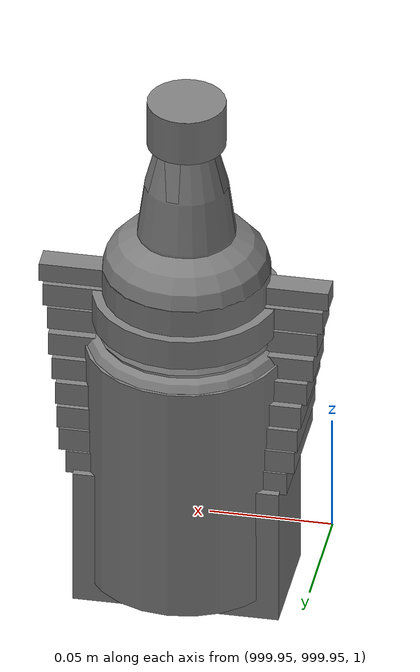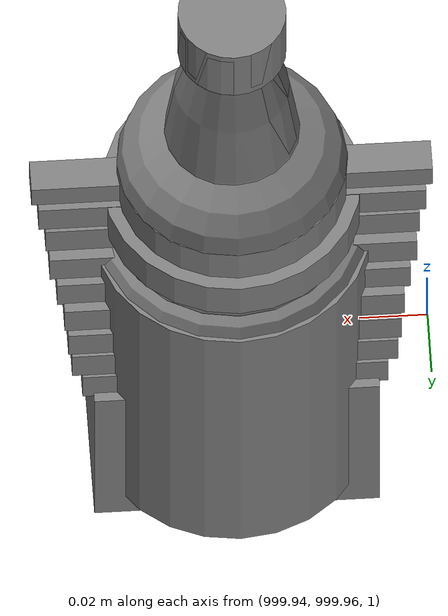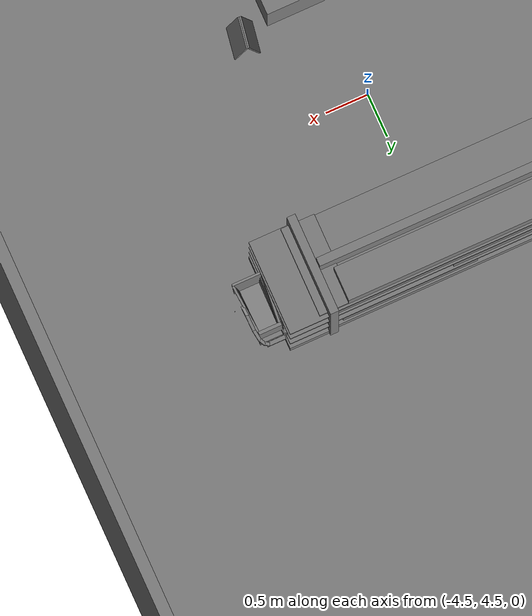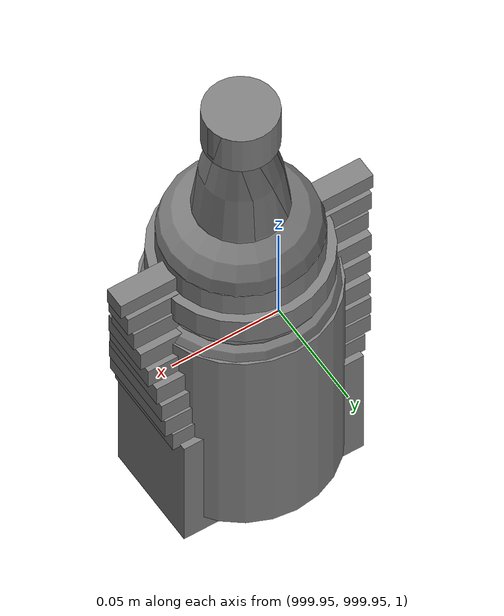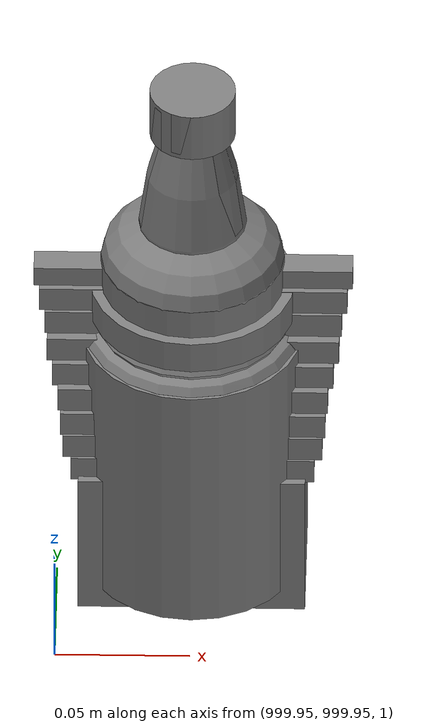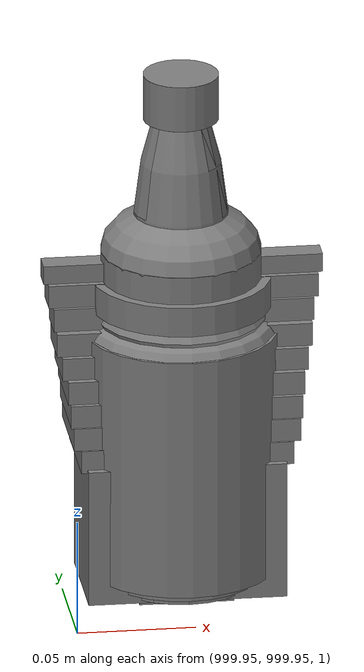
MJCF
<mujoco>
    <option gravity="0.000000000 0.000000000 -9.810000420" timestep="0.0166666" integrator="implicitfast" density="1.225" viscosity="1.8000001e-05" noslip_iterations="10" iterations="100" sdf_iterations="50">
        <flag multiccd="disable"/>
    </option>
    <size memory="1000M"/>
    <compiler coordinate="local"/>
    <worldbody>
        <light cutoff="30" pos="0 1 1" dir="0 -1 -2"/>
        <light cutoff="30" pos="0 -1 1" dir="0 1 -2"/>
        <body pos="0.000000000 0.000000000 0.000000000" euler="0.000000000 0.000000000 0.000000000" name="Interactive Objects_Interactive Objects"/>
        <body pos="1000.000000000 1000.000000000 1.000000000" euler="0.000000000 0.000000000 0.000000000" name="openloong_gripper_2f85_fix_base_usda_jar_01">
            <geom contype="1" conaffinity="1" density="1000" type="box" material="" rgba="0.500000000 0.500000000 0.500000000 1.000000000" solimp="0.899999976 0.949999988 0.001000000" friction="1.000000000 0.005000000 0.000100000" solref="0.020000000 1.000000000" margin="0" condim="3" group="0" pos="0.000000000 0.000000000 0.006158113" quat="1.000000000 0.000000000 0.000000000 0.000000000" size="0.020000000 0.020000000 0.005000000" name="openloong_gripper_2f85_fix_base_usda_geom_EBD5B321_B150_4B0D_BE5C_4103038A7891"/>
            <geom contype="1" conaffinity="1" density="1000" type="cylinder" material="" rgba="0.500000000 0.500000000 0.500000000 1.000000000" solimp="0.899999976 0.949999988 0.001000000" friction="1.000000000 0.005000000 0.000100000" solref="0.020000000 1.000000000" margin="0" condim="3" group="0" pos="0.000000000 0.000000000 0.062744498" quat="1.000000000 0.000000000 0.000000000 0.000000000" size="0.041000001 0.052999999 1.000000000" name="openloong_gripper_2f85_fix_base_usda_geom_D4C826E0_9A8F_4CFD_AD5E_40CD80E28FAF"/>
            <geom contype="1" conaffinity="1" density="1000" type="ellipsoid" material="" rgba="0.500000000 0.500000000 0.500000000 1.000000000" solimp="0.899999976 0.949999988 0.001000000" friction="1.000000000 0.005000000 0.000100000" solref="0.020000000 1.000000000" margin="0" condim="3" group="0" pos="0.000000000 0.000000000 0.122252703" quat="1.000000000 0.000000000 0.000000000 0.000000000" size="0.035999998 0.035999998 0.010000000" name="openloong_gripper_2f85_fix_base_usda_geom_825E416F_120C_4EA3_A041_06109F62E50F"/>
            <geom contype="1" conaffinity="1" density="1000" type="cylinder" material="" rgba="0.500000000 0.500000000 0.500000000 1.000000000" solimp="0.899999976 0.949999988 0.001000000" friction="1.000000000 0.005000000 0.000100000" solref="0.020000000 1.000000000" margin="0" condim="3" group="0" pos="0.000000000 0.000000000 0.015747190" quat="1.000000000 0.000000000 0.000000000 0.000000000" size="0.035000000 0.010000000 1.000000000" name="openloong_gripper_2f85_fix_base_usda_geom_275FB524_95F9_47BD_BAE9_C32F358E481C"/>
            <geom contype="1" conaffinity="1" density="1000" type="ellipsoid" material="" rgba="0.500000000 0.500000000 0.500000000 1.000000000" solimp="0.899999976 0.949999988 0.001000000" friction="1.000000000 0.005000000 0.000100000" solref="0.020000000 1.000000000" margin="0" condim="3" group="0" pos="0.000000000 0.000000000 0.115815401" quat="1.000000000 0.000000000 0.000000000 0.000000000" size="0.039999999 0.039999999 0.010000000" name="openloong_gripper_2f85_fix_base_usda_geom_F5723968_476E_4659_8FB2_675A1BE0E9DA"/>
            <geom contype="1" conaffinity="1" density="1000" type="cylinder" material="" rgba="0.500000000 0.500000000 0.500000000 1.000000000" solimp="0.899999976 0.949999988 0.001000000" friction="1.000000000 0.005000000 0.000100000" solref="0.020000000 1.000000000" margin="0" condim="3" group="0" pos="0.000000000 0.000000000 0.133183479" quat="1.000000000 0.000000000 0.000000000 0.000000000" size="0.037999999 0.006500000 1.000000000" name="openloong_gripper_2f85_fix_base_usda_geom_30C79C5C_BBD5_4AA6_A552_FF01877B0597"/>
            <freejoint name="openloong_gripper_2f85_fix_base_usda_jar_01_joint"/>
            <site size="0.005000000 0.005000000 0.005000000" rgba="0.500000000 0.500000000 0.500000000 1.000000000" pos="0.000000000 0.000000000 0.000000000" quat="1.000000000 0.000000000 0.000000000 0.000000000" group="0" type="sphere" name="openloong_gripper_2f85_fix_base_usda_jar_01site"/>
        </body>
        <body pos="-1.911276579 6.146953106 1.792084098" euler="-88.396949768 -13.564553261 -44.050563812" mocap="true" name="spotlight3_SpotLight"/>
        <body pos="-1.827798247 5.878304005 1.683923483" euler="167.231842041 -32.615612030 -94.815788269" mocap="true" name="spotlight5_SpotLight"/>
        <body pos="-2.178007603 6.244856358 1.843847632" euler="176.619308472 79.348396301 -125.558242798" mocap="true" name="spotlight6_SpotLight"/>
        <body pos="1000.000000000 1000.000000000 1.000000000" euler="0.000000000 0.000000000 0.000000000" name="openloong_gripper_2f85_fix_base_usda_can">
            <geom contype="1" conaffinity="1" density="1000" type="cylinder" material="" rgba="0.500000000 0.500000000 0.500000000 1.000000000" solimp="0.899999976 0.949999988 0.001000000" friction="1.000000000 0.005000000 0.000100000" solref="0.020000000 1.000000000" margin="0" condim="3" group="0" pos="0.000000000 0.000000000 0.079676986" quat="1.000000000 0.000000000 0.000000000 0.000000000" size="0.034000002 0.071999997 1.000000000" name="openloong_gripper_2f85_fix_base_usda_geom_C4094C5F_5D6D_4EB0_958C_58D804D81855"/>
            <geom contype="1" conaffinity="1" density="1000" type="ellipsoid" material="" rgba="0.500000000 0.500000000 0.500000000 1.000000000" solimp="0.899999976 0.949999988 0.001000000" friction="1.000000000 0.005000000 0.000100000" solref="0.020000000 1.000000000" margin="0" condim="3" group="0" pos="0.000000000 0.000000000 0.151854277" quat="1.000000000 0.000000000 0.000000000 0.000000000" size="0.034000002 0.034000002 0.020000000" name="openloong_gripper_2f85_fix_base_usda_geom_AC9AA2D4_94E1_4761_927F_1E0765184339"/>
            <geom contype="1" conaffinity="1" density="1000" type="box" material="" rgba="0.500000000 0.500000000 0.500000000 1.000000000" solimp="0.899999976 0.949999988 0.001000000" friction="1.000000000 0.005000000 0.000100000" solref="0.020000000 1.000000000" margin="0" condim="3" group="0" pos="0.000000000 0.000000000 0.004777670" quat="1.000000000 0.000000000 0.000000000 0.000000000" size="0.020000000 0.020000000 0.005000000" name="openloong_gripper_2f85_fix_base_usda_geom_6F6B58CF_FC9B_49DD_B028_BFD9BB920CA0"/>
            <freejoint name="openloong_gripper_2f85_fix_base_usda_can_joint"/>
            <site size="0.005000000 0.005000000 0.005000000" rgba="0.500000000 0.500000000 0.500000000 1.000000000" pos="0.000000000 0.000000000 0.000000000" quat="1.000000000 0.000000000 0.000000000 0.000000000" group="0" type="sphere" name="openloong_gripper_2f85_fix_base_usda_cansite"/>
        </body>
        <body pos="1000.000000000 1000.000000000 1.000000000" euler="0.000000000 0.000000000 0.000000000" name="openloong_gripper_2f85_fix_base_usda_bottle_blue">
            <geom contype="1" conaffinity="1" density="1000" type="ellipsoid" material="" rgba="0.500000000 0.500000000 0.500000000 1.000000000" solimp="0.899999976 0.949999988 0.001000000" friction="1.000000000 0.005000000 0.000100000" solref="0.020000000 1.000000000" margin="0" condim="3" group="0" pos="0.000000000 0.000000000 0.118920922" quat="1.000000000 0.000000000 0.000000000 0.000000000" size="0.030999999 0.030999999 0.029999999" name="openloong_gripper_2f85_fix_base_usda_geom_4D50FCA3_F644_47D0_9146_A43D9A58F72A"/>
            <geom contype="1" conaffinity="1" density="1000" type="box" material="" rgba="0.500000000 0.500000000 0.500000000 1.000000000" solimp="0.899999976 0.949999988 0.001000000" friction="1.000000000 0.005000000 0.000100000" solref="0.020000000 1.000000000" margin="0" condim="3" group="0" pos="0.000000000 0.000000000 0.002164602" quat="1.000000000 0.000000000 0.000000000 0.000000000" size="0.020000000 0.020000000 0.003000000" name="openloong_gripper_2f85_fix_base_usda_geom_D1CC73CF_34C2_44AE_9FBC_698BAA912CB0"/>
            <geom contype="1" conaffinity="1" density="1000" type="cylinder" material="" rgba="0.500000000 0.500000000 0.500000000 1.000000000" solimp="0.899999976 0.949999988 0.001000000" friction="1.000000000 0.005000000 0.000100000" solref="0.020000000 1.000000000" margin="0" condim="3" group="0" pos="0.000000000 -0.000366211 0.060859680" quat="1.000000000 0.000000000 0.000000000 0.000000000" size="0.030999999 0.057999998 1.000000000" name="openloong_gripper_2f85_fix_base_usda_geom_9939E20D_F670_4DC9_BA3B_046629FB5702"/>
            <geom contype="1" conaffinity="1" density="1000" type="cylinder" material="" rgba="0.500000000 0.500000000 0.500000000 1.000000000" solimp="0.899999976 0.949999988 0.001000000" friction="1.000000000 0.005000000 0.000100000" solref="0.020000000 1.000000000" margin="0" condim="3" group="0" pos="0.000000000 0.000000000 0.220594406" quat="1.000000000 0.000000000 0.000000000 0.000000000" size="0.016000001 0.010000000 1.000000000" name="openloong_gripper_2f85_fix_base_usda_geom_A6ACE30C_CF0C_491D_A391_BDCB9512F2C6"/>
            <geom contype="1" conaffinity="1" density="1000" type="ellipsoid" material="" rgba="0.500000000 0.500000000 0.500000000 1.000000000" solimp="0.899999976 0.949999988 0.001000000" friction="1.000000000 0.005000000 0.000100000" solref="0.020000000 1.000000000" margin="0" condim="3" group="0" pos="0.000000000 0.000000000 0.144259930" quat="1.000000000 0.000000000 0.000000000 0.000000000" size="0.021000000 0.021000000 0.079999998" name="openloong_gripper_2f85_fix_base_usda_geom_98079ACE_6B6D_415A_96EA_27A7371960BB"/>
            <freejoint name="openloong_gripper_2f85_fix_base_usda_bottle_blue_joint"/>
            <site size="0.005000000 0.005000000 0.005000000" rgba="0.500000000 0.500000000 0.500000000 1.000000000" pos="0.000000000 0.000000000 0.000000000" quat="0.999961913 0.008726535 0.000000000 0.000000000" group="0" type="sphere" name="openloong_gripper_2f85_fix_base_usda_bottle_bluesite"/>
        </body>
        <body pos="1000.000000000 1000.000000000 1.000000000" euler="0.000000000 0.000000000 0.000000000" name="openloong_gripper_2f85_fix_base_usda_salt">
            <geom contype="1" conaffinity="1" density="1000" type="box" material="" rgba="0.500000000 0.500000000 0.500000000 1.000000000" solimp="0.899999976 0.949999988 0.001000000" friction="1.000000000 0.005000000 0.000100000" solref="0.020000000 1.000000000" margin="0" condim="3" group="0" pos="0.000305176 0.000000000 0.084862232" quat="1.000000000 0.000000000 0.000000000 0.000000000" size="0.048999999 0.018999999 0.005000000" name="openloong_gripper_2f85_fix_base_usda_geom_EEE92AE1_1C11_4038_BBC6_31E21734563F"/>
            <geom contype="1" conaffinity="1" density="1000" type="box" material="" rgba="0.500000000 0.500000000 0.500000000 1.000000000" solimp="0.899999976 0.949999988 0.001000000" friction="1.000000000 0.005000000 0.000100000" solref="0.020000000 1.000000000" margin="0" condim="3" group="0" pos="0.000305176 0.000000000 0.104564309" quat="1.000000000 0.000000000 0.000000000 0.000000000" size="0.052000001 0.014000000 0.005000000" name="openloong_gripper_2f85_fix_base_usda_geom_7F9DB53B_F57E_45E8_BCDB_2EDF24FE497C"/>
            <geom contype="1" conaffinity="1" density="1000" type="box" material="" rgba="0.500000000 0.500000000 0.500000000 1.000000000" solimp="0.899999976 0.949999988 0.001000000" friction="1.000000000 0.005000000 0.000100000" solref="0.020000000 1.000000000" margin="0" condim="3" group="0" pos="0.000305176 0.000000000 0.114487171" quat="1.000000000 0.000000000 0.000000000 0.000000000" size="0.054000001 0.011500000 0.005000000" name="openloong_gripper_2f85_fix_base_usda_geom_DAA2E076_2E0E_49FC_81B1_522097E7D7D4"/>
            <geom contype="1" conaffinity="1" density="1000" type="box" material="" rgba="0.500000000 0.500000000 0.500000000 1.000000000" solimp="0.899999976 0.949999988 0.001000000" friction="1.000000000 0.005000000 0.000100000" solref="0.020000000 1.000000000" margin="0" condim="3" group="0" pos="0.000305176 0.000000000 0.075103164" quat="1.000000000 0.000000000 0.000000000 0.000000000" size="0.048000000 0.020000000 0.005000000" name="openloong_gripper_2f85_fix_base_usda_geom_AD40DA8A_AF14_47CB_959B_6A23CE1FBCDB"/>
            <geom contype="1" conaffinity="1" density="1000" type="box" material="" rgba="0.500000000 0.500000000 0.500000000 1.000000000" solimp="0.899999976 0.949999988 0.001000000" friction="1.000000000 0.005000000 0.000100000" solref="0.020000000 1.000000000" margin="0" condim="3" group="0" pos="0.000305176 0.000000000 0.134892464" quat="1.000000000 0.000000000 0.000000000 0.000000000" size="0.057000000 0.007000000 0.005000000" name="openloong_gripper_2f85_fix_base_usda_geom_1182A828_4666_4E81_9BF4_DDA2849B652A"/>
            <geom contype="1" conaffinity="1" density="1000" type="box" material="" rgba="0.500000000 0.500000000 0.500000000 1.000000000" solimp="0.899999976 0.949999988 0.001000000" friction="1.000000000 0.005000000 0.000100000" solref="0.020000000 1.000000000" margin="0" condim="3" group="0" pos="0.000305176 0.000000000 0.094920278" quat="1.000000000 0.000000000 0.000000000 0.000000000" size="0.050000001 0.017000001 0.005000000" name="openloong_gripper_2f85_fix_base_usda_geom_A516F109_572E_4027_B716_BB5A514F2DC2"/>
            <geom contype="1" conaffinity="1" density="1000" type="box" material="" rgba="0.500000000 0.500000000 0.500000000 1.000000000" solimp="0.899999976 0.949999988 0.001000000" friction="1.000000000 0.005000000 0.000100000" solref="0.020000000 1.000000000" margin="0" condim="3" group="0" pos="0.000305176 0.000000000 0.065204859" quat="1.000000000 0.000000000 0.000000000 0.000000000" size="0.045000002 0.021000000 0.005000000" name="openloong_gripper_2f85_fix_base_usda_geom_CEA7D90E_2500_449F_9231_E034925B0F77"/>
            <geom contype="1" conaffinity="1" density="1000" type="box" material="" rgba="0.500000000 0.500000000 0.500000000 1.000000000" solimp="0.899999976 0.949999988 0.001000000" friction="1.000000000 0.005000000 0.000100000" solref="0.020000000 1.000000000" margin="0" condim="3" group="0" pos="0.000305176 0.000000000 0.144135714" quat="1.000000000 0.000000000 0.000000000 0.000000000" size="0.059000000 0.005000000 0.004000000" name="openloong_gripper_2f85_fix_base_usda_geom_4ED683C7_72A9_4E0A_A9B5_CAB1A971EB17"/>
            <geom contype="1" conaffinity="1" density="1000" type="box" material="" rgba="0.500000000 0.500000000 0.500000000 1.000000000" solimp="0.899999976 0.949999988 0.001000000" friction="1.000000000 0.005000000 0.000100000" solref="0.020000000 1.000000000" margin="0" condim="3" group="0" pos="0.000000000 0.000000000 0.031593561" quat="1.000000000 0.000000000 0.000000000 0.000000000" size="0.041999999 0.024000000 0.029999999" name="openloong_gripper_2f85_fix_base_usda_geom_96517502_6F30_498A_9331_91F53895E9E4"/>
            <geom contype="1" conaffinity="1" density="1000" type="box" material="" rgba="0.500000000 0.500000000 0.500000000 1.000000000" solimp="0.899999976 0.949999988 0.001000000" friction="1.000000000 0.005000000 0.000100000" solref="0.020000000 1.000000000" margin="0" condim="3" group="0" pos="0.000305176 0.000000000 0.124608755" quat="1.000000000 0.000000000 0.000000000 0.000000000" size="0.055000000 0.008000000 0.005000000" name="openloong_gripper_2f85_fix_base_usda_geom_6E985237_6C91_445B_A454_F15BB453E2EE"/>
            <freejoint name="openloong_gripper_2f85_fix_base_usda_salt_joint"/>
            <site size="0.005000000 0.005000000 0.005000000" rgba="0.500000000 0.500000000 0.500000000 1.000000000" pos="0.000000000 0.000000000 0.000000000" quat="1.000000000 0.000000000 0.000000000 0.000000000" group="0" type="sphere" name="openloong_gripper_2f85_fix_base_usda_saltsite"/>
        </body>
        <body pos="1000.000000000 1000.000000000 1.000000000" euler="0.000000000 0.000000000 0.000000000" name="openloong_gripper_2f85_fix_base_usda_bottle_red">
            <geom contype="1" conaffinity="1" density="1000" type="ellipsoid" material="" rgba="0.500000000 0.500000000 0.500000000 1.000000000" solimp="0.899999976 0.949999988 0.001000000" friction="1.000000000 0.005000000 0.000100000" solref="0.020000000 1.000000000" margin="0" condim="3" group="0" pos="0.000000000 0.000000000 0.144284487" quat="1.000000000 0.000000000 0.000000000 0.000000000" size="0.021000000 0.021000000 0.079999998" name="openloong_gripper_2f85_fix_base_usda_geom_A1369D88_276A_43AC_83FF_8D58A7160672"/>
            <geom contype="1" conaffinity="1" density="1000" type="cylinder" material="" rgba="0.500000000 0.500000000 0.500000000 1.000000000" solimp="0.899999976 0.949999988 0.001000000" friction="1.000000000 0.005000000 0.000100000" solref="0.020000000 1.000000000" margin="0" condim="3" group="0" pos="0.000000000 0.000000000 0.220618963" quat="1.000000000 0.000000000 0.000000000 0.000000000" size="0.016000001 0.010000000 1.000000000" name="openloong_gripper_2f85_fix_base_usda_geom_84CFF0AD_7F36_4C8C_B63C_4054A35C56E3"/>
            <geom contype="1" conaffinity="1" density="1000" type="ellipsoid" material="" rgba="0.500000000 0.500000000 0.500000000 1.000000000" solimp="0.899999976 0.949999988 0.001000000" friction="1.000000000 0.005000000 0.000100000" solref="0.020000000 1.000000000" margin="0" condim="3" group="0" pos="0.000000000 0.000000000 0.118945479" quat="1.000000000 0.000000000 0.000000000 0.000000000" size="0.030999999 0.030999999 0.029999999" name="openloong_gripper_2f85_fix_base_usda_geom_9A62870E_A316_4C8F_8415_EB03E95CCCB9"/>
            <geom contype="1" conaffinity="1" density="1000" type="box" material="" rgba="0.500000000 0.500000000 0.500000000 1.000000000" solimp="0.899999976 0.949999988 0.001000000" friction="1.000000000 0.005000000 0.000100000" solref="0.020000000 1.000000000" margin="0" condim="3" group="0" pos="0.000000000 0.000000000 0.002189159" quat="1.000000000 0.000000000 0.000000000 0.000000000" size="0.020000000 0.020000000 0.003000000" name="openloong_gripper_2f85_fix_base_usda_geom_D83AFB0C_231B_4CDF_995E_1B79E76A68A7"/>
            <geom contype="1" conaffinity="1" density="1000" type="cylinder" material="" rgba="0.500000000 0.500000000 0.500000000 1.000000000" solimp="0.899999976 0.949999988 0.001000000" friction="1.000000000 0.005000000 0.000100000" solref="0.020000000 1.000000000" margin="0" condim="3" group="0" pos="0.000000000 -0.000366211 0.060884237" quat="1.000000000 0.000000000 0.000000000 0.000000000" size="0.030999999 0.057999998 1.000000000" name="openloong_gripper_2f85_fix_base_usda_geom_6EA48EFA_2912_42B3_ABE6_D33DAC7222C5"/>
            <freejoint name="openloong_gripper_2f85_fix_base_usda_bottle_red_joint"/>
            <site size="0.005000000 0.005000000 0.005000000" rgba="0.500000000 0.500000000 0.500000000 1.000000000" pos="0.000000000 0.000000000 0.000000000" quat="0.999961913 0.008726535 0.000000000 0.000000000" group="0" type="sphere" name="openloong_gripper_2f85_fix_base_usda_bottle_redsite"/>
        </body>
        <body pos="0.000000000 0.000000000 0.000000000" euler="0.000000000 0.000000000 0.000000000" name=" Static Objects_ Static Objects">
            <geom contype="1" conaffinity="1" density="1000" type="box" material="" rgba="0.500000000 0.500000000 0.500000000 1.000000000" solimp="0.899999976 0.949999988 0.001000000" friction="1.000000000 0.005000000 0.000100000" solref="0.020000000 1.000000000" margin="0" condim="3" group="0" pos="-6.286010742 6.153595448 1.563861728" quat="0.707107067 0.000000000 0.000000000 0.707106471" size="0.529999971 3.134999990 0.025000000" name=" Static Objects_geom_D5D8915A_57AC_4521_AAE2_2E7D4F7F79D6"/>
            <geom contype="1" conaffinity="1" density="1000" type="box" material="" rgba="0.500000000 0.500000000 0.500000000 1.000000000" solimp="0.899999976 0.949999988 0.001000000" friction="1.000000000 0.005000000 0.000100000" solref="0.020000000 1.000000000" margin="0" condim="3" group="0" pos="-3.101639986 6.150595188 1.018643856" quat="1.000000000 0.000000000 0.000000000 0.000000000" size="0.050000001 0.579999983 1.019999981" name=" Static Objects_geom_97EDB52F_E505_4F5B_B0A7_A6116D4CFB4E"/>
            <geom contype="1" conaffinity="1" density="1000" type="box" material="" rgba="0.500000000 0.500000000 0.500000000 1.000000000" solimp="0.899999976 0.949999988 0.001000000" friction="1.000000000 0.005000000 0.000100000" solref="0.020000000 1.000000000" margin="0" condim="3" group="0" pos="-2.825197220 6.153595448 1.563861728" quat="0.707107067 0.000000000 0.000000000 0.707106471" size="0.550000012 0.239999995 0.025000000" name=" Static Objects_geom_C4E3CFF8_C666_4944_AF13_830BEC6CDA44"/>
            <geom contype="1" conaffinity="1" density="1000" type="box" material="" rgba="0.500000000 0.500000000 0.500000000 1.000000000" solimp="0.899999976 0.949999988 0.001000000" friction="1.000000000 0.005000000 0.000100000" solref="0.020000000 1.000000000" margin="0" condim="3" group="0" pos="-6.311686516 6.153595448 1.018643856" quat="0.707107067 0.000000000 0.000000000 0.707106471" size="0.050000001 3.150000095 1.019999981" name=" Static Objects_geom_FD98D06D_8EDC_4BD5_B11D_4D9515C72651"/>
            <geom contype="1" conaffinity="1" density="1000" type="box" material="" rgba="0.500000000 0.500000000 0.500000000 1.000000000" solimp="0.899999976 0.949999988 0.001000000" friction="1.000000000 0.005000000 0.000100000" solref="0.020000000 1.000000000" margin="0" condim="3" group="0" pos="-2.825197220 6.153595448 1.115278244" quat="0.707107067 0.000000000 0.000000000 0.707106471" size="0.550000012 0.239999995 0.025000000" name=" Static Objects_geom_E08418C7_C652_48C8_AD8D_B4B67C4A420F"/>
            <geom contype="1" conaffinity="1" density="1000" type="box" material="" rgba="0.500000000 0.500000000 0.500000000 1.000000000" solimp="0.899999976 0.949999988 0.001000000" friction="1.000000000 0.005000000 0.000100000" solref="0.020000000 1.000000000" margin="0" condim="3" group="0" pos="-6.293097973 6.153595448 1.114443064" quat="0.707107067 0.000000000 0.000000000 0.707106471" size="0.529999971 3.134999990 0.025000000" name=" Static Objects_geom_0746FA06_D50D_4802_A289_0407F600001A"/>
            <geom contype="1" conaffinity="1" density="1000" type="box" material="" rgba="0.500000000 0.500000000 0.500000000 1.000000000" solimp="0.899999976 0.949999988 0.001000000" friction="1.000000000 0.005000000 0.000100000" solref="0.020000000 1.000000000" margin="0" condim="3" group="0" pos="-2.825197220 6.153595448 0.629031777" quat="0.707107067 0.000000000 0.000000000 0.707106471" size="0.550000012 0.239999995 0.025000000" name=" Static Objects_geom_EB23EF68_B0C0_4D77_A975_37A07B9B473F"/>
            <geom contype="1" conaffinity="1" density="1000" type="box" material="" rgba="0.500000000 0.500000000 0.500000000 1.000000000" solimp="0.899999976 0.949999988 0.001000000" friction="1.000000000 0.005000000 0.000100000" solref="0.020000000 1.000000000" margin="0" condim="3" group="0" pos="-6.286010742 6.153595448 0.096129179" quat="0.707107067 0.000000000 0.000000000 0.707106471" size="0.529999971 3.134999990 0.098999999" name=" Static Objects_geom_A15BB65C_F31F_4599_93FD_68B972E4C313"/>
            <geom contype="1" conaffinity="1" density="1000" type="box" material="" rgba="0.500000000 0.500000000 0.500000000 1.000000000" solimp="0.899999976 0.949999988 0.001000000" friction="1.000000000 0.005000000 0.000100000" solref="0.020000000 1.000000000" margin="0" condim="3" group="0" pos="-2.825197220 6.153595448 0.097434282" quat="0.707107067 0.000000000 0.000000000 0.707106471" size="0.550000012 0.239999995 0.098999999" name=" Static Objects_geom_CC3F49B2_7AB2_4A25_A5E5_DB901984315B"/>
            <geom contype="1" conaffinity="1" density="1000" type="box" material="" rgba="0.500000000 0.500000000 0.500000000 1.000000000" solimp="0.899999976 0.949999988 0.001000000" friction="1.000000000 0.005000000 0.000100000" solref="0.020000000 1.000000000" margin="0" condim="3" group="0" pos="-6.286010742 6.153595448 0.629031777" quat="0.707107067 0.000000000 0.000000000 0.707106471" size="0.529999971 3.134999990 0.025000000" name=" Static Objects_geom_7ECF9DBD_862C_4FDC_A921_3109963BD060"/>
            <geom contype="1" conaffinity="1" density="1000" type="box" material="" rgba="0.500000000 0.500000000 0.500000000 1.000000000" solimp="0.899999976 0.949999988 0.001000000" friction="1.000000000 0.005000000 0.000100000" solref="0.020000000 1.000000000" margin="0" condim="3" group="0" pos="-6.000000000 20.159999847 2.000000000" quat="1.000000000 0.000000000 0.000000000 0.000000000" size="6.079999924 0.070000000 2.000000000" name=" Static Objects_geom_AC60AD48_2493_41D2_AB05_C8295E075172"/>
            <geom contype="1" conaffinity="1" density="1000" type="box" material="" rgba="0.500000000 0.500000000 0.500000000 1.000000000" solimp="0.899999976 0.949999988 0.001000000" friction="1.000000000 0.005000000 0.000100000" solref="0.020000000 1.000000000" margin="0" condim="3" group="0" pos="-6.000000000 0.035000000 2.000000000" quat="1.000000000 0.000000000 0.000000000 0.000000000" size="6.079999924 0.070000000 2.000000000" name=" Static Objects_geom_D325ABB9_BB89_40CB_A2DF_09FAAD49ADD9"/>
            <geom contype="1" conaffinity="1" density="1000" type="box" material="" rgba="0.500000000 0.500000000 0.500000000 1.000000000" solimp="0.899999976 0.949999988 0.001000000" friction="1.000000000 0.005000000 0.000100000" solref="0.020000000 1.000000000" margin="0" condim="3" group="0" pos="0.000000000 10.000000000 2.000000000" quat="1.000000000 0.000000000 0.000000000 0.000000000" size="0.070000000 10.500000000 2.000000000" name=" Static Objects_geom_9763E052_78F0_4647_8191_45653294DB11"/>
            <geom contype="1" conaffinity="1" density="1000" type="box" material="" rgba="0.500000000 0.500000000 0.500000000 1.000000000" solimp="0.899999976 0.949999988 0.001000000" friction="1.000000000 0.005000000 0.000100000" solref="0.020000000 1.000000000" margin="0" condim="3" group="0" pos="-12.050000191 10.000000000 2.000000000" quat="1.000000000 0.000000000 0.000000000 0.000000000" size="0.070000000 10.500000000 2.000000000" name=" Static Objects_geom_367B42BA_3E8F_47AD_BBAC_B08F2D93CF88"/>
            <geom contype="1" conaffinity="1" density="1000" type="plane" material="" rgba="0.500000000 0.500000000 0.500000000 1.000000000" solimp="0.899999976 0.949999988 0.001000000" friction="1.000000000 0.005000000 0.000100000" solref="0.020000000 1.000000000" margin="0" condim="3" group="0" pos="-6.000000000 10.399999619 0.000000000" quat="1.000000000 0.000000000 0.000000000 0.000000000" size="6.050000191 10.800000191 0.010000000" name=" Static Objects_geom_A9B56E5B_5B62_4B3C_B0F0_090FFC080B9C"/>
            <geom contype="1" conaffinity="1" density="1000" type="box" material="" rgba="0.500000000 0.500000000 0.500000000 1.000000000" solimp="0.899999976 0.949999988 0.001000000" friction="1.000000000 0.005000000 0.000100000" solref="0.020000000 1.000000000" margin="0" condim="3" group="0" pos="-8.830721855 2.096410990 0.549305558" quat="1.000000000 0.000000000 0.000000000 0.000000000" size="0.280000001 0.430000007 0.550000012" name=" Static Objects_geom_67CC981F_7879_4E00_AB2B_C73378147513"/>
            <geom contype="1" conaffinity="1" density="1000" type="box" material="" rgba="0.500000000 0.500000000 0.500000000 1.000000000" solimp="0.899999976 0.949999988 0.001000000" friction="1.000000000 0.005000000 0.000100000" solref="0.020000000 1.000000000" margin="0" condim="3" group="0" pos="-6.460197449 2.937205315 0.548931718" quat="1.000000000 0.000000000 0.000000000 0.000000000" size="2.650000095 0.430000007 0.550000012" name=" Static Objects_geom_40E4EC30_5623_49F6_864E_EC0B30FDD47E"/>
            <geom contype="1" conaffinity="1" density="1000" type="box" material="" rgba="0.500000000 0.500000000 0.500000000 1.000000000" solimp="0.899999976 0.949999988 0.001000000" friction="1.000000000 0.005000000 0.000100000" solref="0.020000000 1.000000000" margin="0" condim="3" group="0" pos="-4.240264893 1.327049494 0.549888909" quat="1.000000000 0.000000000 0.000000000 0.000000000" size="0.430000007 1.200000048 0.550000012" name=" Static Objects_geom_D30801FC_D985_4689_9F81_17DB8397D2F2"/>
            <geom contype="1" conaffinity="1" density="1000" type="box" material="" rgba="0.500000000 0.500000000 0.500000000 1.000000000" solimp="0.899999976 0.949999988 0.001000000" friction="1.000000000 0.005000000 0.000100000" solref="0.020000000 1.000000000" margin="0" condim="3" group="0" pos="-7.408766270 3.088089943 1.776644945" quat="0.928051054 0.000000000 0.000000000 0.372453064" size="0.050000001 0.100000001 0.050000001" name=" Static Objects_geom_EC304E92_C472_4660_ABFA_E0C274B4FEDE"/>
            <geom contype="1" conaffinity="1" density="1000" type="box" material="" rgba="0.500000000 0.500000000 0.500000000 1.000000000" solimp="0.899999976 0.949999988 0.001000000" friction="1.000000000 0.005000000 0.000100000" solref="0.020000000 1.000000000" margin="0" condim="3" group="0" pos="-7.437745571 3.067511320 1.289965630" quat="1.000000000 0.000000000 0.000000000 0.000000000" size="0.029999999 0.020000000 0.020000000" name=" Static Objects_geom_46022A44_CF48_46CD_A0EE_A530ECD7C59C"/>
            <geom contype="1" conaffinity="1" density="1000" type="box" material="" rgba="0.500000000 0.500000000 0.500000000 1.000000000" solimp="0.899999976 0.949999988 0.001000000" friction="1.000000000 0.005000000 0.000100000" solref="0.020000000 1.000000000" margin="0" condim="3" group="0" pos="-7.719123363 2.867671013 1.173410416" quat="1.000000000 0.000000000 0.000000000 0.000000000" size="0.250000000 0.250000000 0.079999998" name=" Static Objects_geom_1B84603A_00FF_4658_B6FD_5D46BF5ED3F7"/>
            <geom contype="1" conaffinity="1" density="1000" type="box" material="" rgba="0.500000000 0.500000000 0.500000000 1.000000000" solimp="0.899999976 0.949999988 0.001000000" friction="1.000000000 0.005000000 0.000100000" solref="0.020000000 1.000000000" margin="0" condim="3" group="0" pos="-7.719123363 2.958004713 1.530241251" quat="1.000000000 0.000000000 0.000000000 0.000000000" size="0.250000000 0.159999996 0.280000001" name=" Static Objects_geom_3E9E71CB_D7DE_4F76_ACBB_E3472C7D6061"/>
            <geom contype="1" conaffinity="1" density="1000" type="cylinder" material="" rgba="0.500000000 0.500000000 0.500000000 1.000000000" solimp="0.899999976 0.949999988 0.001000000" friction="1.000000000 0.005000000 0.000100000" solref="0.020000000 1.000000000" margin="0" condim="3" group="0" pos="-7.427312374 3.069516420 1.502544641" quat="0.928051054 0.000000000 0.000000000 0.372453064" size="0.015000000 0.230000004 0.100000001" name=" Static Objects_geom_6611589D_0D4F_45AC_B244_FB4B1353E057"/>
            <geom contype="1" conaffinity="1" density="1000" type="box" material="" rgba="0.500000000 0.500000000 0.500000000 1.000000000" solimp="0.899999976 0.949999988 0.001000000" friction="1.000000000 0.005000000 0.000100000" solref="0.020000000 1.000000000" margin="0" condim="3" group="0" pos="-9.058088303 6.434794426 1.209077358" quat="1.000000000 0.000000000 0.000000000 0.000000000" size="0.250000000 0.100000001 0.070000000" name=" Static Objects_geom_EB925841_16D2_44F7_985D_10FA42E5A76F"/>
            <geom contype="1" conaffinity="1" density="1000" type="box" material="" rgba="0.500000000 0.500000000 0.500000000 1.000000000" solimp="0.899999976 0.949999988 0.001000000" friction="1.000000000 0.005000000 0.000100000" solref="0.020000000 1.000000000" margin="0" condim="3" group="0" pos="-5.611940861 6.318420410 0.350975692" quat="1.000000000 0.000000000 0.000000000 0.000000000" size="0.699999988 0.100000001 0.150000006" name=" Static Objects_geom_33DE1A49_5FA6_4979_91FD_AACF3CD9499D"/>
            <geom contype="1" conaffinity="1" density="1000" type="box" material="" rgba="0.500000000 0.500000000 0.500000000 1.000000000" solimp="0.899999976 0.949999988 0.001000000" friction="1.000000000 0.005000000 0.000100000" solref="0.020000000 1.000000000" margin="0" condim="3" group="0" pos="-9.237723351 6.464855671 1.209077358" quat="1.000000000 0.000000000 0.000000000 0.000000000" size="0.100000001 0.100000001 0.070000000" name=" Static Objects_geom_FA9BA933_5E5F_499C_8152_B42AC331A38B"/>
            <geom contype="1" conaffinity="1" density="1000" type="box" material="" rgba="0.500000000 0.500000000 0.500000000 1.000000000" solimp="0.899999976 0.949999988 0.001000000" friction="1.000000000 0.005000000 0.000100000" solref="0.020000000 1.000000000" margin="0" condim="3" group="0" pos="-6.300771236 6.459744930 1.744376063" quat="1.000000000 0.000000000 0.000000000 0.000000000" size="3.000000000 0.200000003 0.150000006" name=" Static Objects_geom_425F5FD8_0045_4745_9D9B_537848623C2B"/>
            <geom contype="1" conaffinity="1" density="1000" type="box" material="" rgba="0.500000000 0.500000000 0.500000000 1.000000000" solimp="0.899999976 0.949999988 0.001000000" friction="1.000000000 0.005000000 0.000100000" solref="0.020000000 1.000000000" margin="0" condim="3" group="0" pos="-7.373087406 6.458900928 1.214329123" quat="1.000000000 0.000000000 0.000000000 0.000000000" size="0.250000000 0.200000003 0.075000003" name=" Static Objects_geom_F7ED098E_43F4_405A_BB71_03A0F3740FDB"/>
            <geom contype="1" conaffinity="1" density="1000" type="box" material="" rgba="0.500000000 0.500000000 0.500000000 1.000000000" solimp="0.899999976 0.949999988 0.001000000" friction="1.000000000 0.005000000 0.000100000" solref="0.020000000 1.000000000" margin="0" condim="3" group="0" pos="-4.035642624 6.459744930 0.352518857" quat="1.000000000 0.000000000 0.000000000 0.000000000" size="0.800000012 0.200000003 0.150000006" name=" Static Objects_geom_80ED6D59_47BD_4A86_8829_019C0AF89FDC"/>
            <geom contype="1" conaffinity="1" density="1000" type="box" material="" rgba="0.500000000 0.500000000 0.500000000 1.000000000" solimp="0.899999976 0.949999988 0.001000000" friction="1.000000000 0.005000000 0.000100000" solref="0.020000000 1.000000000" margin="0" condim="3" group="0" pos="-3.907610416 6.318625927 0.800981164" quat="1.000000000 0.000000000 0.000000000 0.000000000" size="0.500000000 0.100000001 0.150000006" name=" Static Objects_geom_B4EE9E6B_8A3F_421D_9D49_D6B9477CACCC"/>
            <geom contype="1" conaffinity="1" density="1000" type="box" material="" rgba="0.500000000 0.500000000 0.500000000 1.000000000" solimp="0.899999976 0.949999988 0.001000000" friction="1.000000000 0.005000000 0.000100000" solref="0.020000000 1.000000000" margin="0" condim="3" group="0" pos="-6.098561764 6.327973843 1.292199373" quat="1.000000000 0.000000000 0.000000000 0.000000000" size="0.500000000 0.100000001 0.150000006" name=" Static Objects_geom_79FE6951_BCDD_493C_94CE_76839BCA41A4"/>
            <geom contype="1" conaffinity="1" density="1000" type="box" material="" rgba="0.500000000 0.500000000 0.500000000 1.000000000" solimp="0.899999976 0.949999988 0.001000000" friction="1.000000000 0.005000000 0.000100000" solref="0.020000000 1.000000000" margin="0" condim="3" group="0" pos="-7.886891365 6.459744930 0.352518857" quat="1.000000000 0.000000000 0.000000000 0.000000000" size="1.500000000 0.200000003 0.150000006" name=" Static Objects_geom_63D5BF74_A2B4_44C9_B3B6_65B64EF6E331"/>
            <geom contype="1" conaffinity="1" density="1000" type="box" material="" rgba="0.500000000 0.500000000 0.500000000 1.000000000" solimp="0.899999976 0.949999988 0.001000000" friction="1.000000000 0.005000000 0.000100000" solref="0.020000000 1.000000000" margin="0" condim="3" group="0" pos="-6.824534416 6.447464466 1.212718010" quat="1.000000000 0.000000000 0.000000000 0.000000000" size="0.100000001 0.100000001 0.075000003" name=" Static Objects_geom_B6F4FA3E_8FDD_4D6E_B932_21775AD62F16"/>
            <geom contype="1" conaffinity="1" density="1000" type="box" material="" rgba="0.500000000 0.500000000 0.500000000 1.000000000" solimp="0.899999976 0.949999988 0.001000000" friction="1.000000000 0.005000000 0.000100000" solref="0.020000000 1.000000000" margin="0" condim="3" group="0" pos="-4.407354832 6.459744930 1.292199373" quat="1.000000000 0.000000000 0.000000000 0.000000000" size="1.240000010 0.200000003 0.150000006" name=" Static Objects_geom_35F4342E_F52A_4A44_B4E4_8AE24E56FB36"/>
            <geom contype="1" conaffinity="1" density="1000" type="box" material="" rgba="0.500000000 0.500000000 0.500000000 1.000000000" solimp="0.899999976 0.949999988 0.001000000" friction="1.000000000 0.005000000 0.000100000" solref="0.020000000 1.000000000" margin="0" condim="3" group="0" pos="-6.751636982 6.459744930 0.800981164" quat="1.000000000 0.000000000 0.000000000 0.000000000" size="2.200000048 0.200000003 0.150000006" name=" Static Objects_geom_4C7A29A3_00E5_4A23_83D4_13DA195C9F50"/>
            <geom contype="1" conaffinity="1" density="1000" type="box" material="" rgba="0.500000000 0.500000000 0.500000000 1.000000000" solimp="0.899999976 0.949999988 0.001000000" friction="1.000000000 0.005000000 0.000100000" solref="0.020000000 1.000000000" margin="0" condim="3" group="0" pos="-6.924745083 6.362090111 1.214329123" quat="1.000000000 0.000000000 0.000000000 0.000000000" size="0.200000003 0.100000001 0.075000003" name=" Static Objects_geom_D2A0248B_BB10_425A_8A49_428B610AF8CC"/>
            <geom contype="1" conaffinity="1" density="1000" type="box" material="" rgba="0.500000000 0.500000000 0.500000000 1.000000000" solimp="0.899999976 0.949999988 0.001000000" friction="1.000000000 0.005000000 0.000100000" solref="0.020000000 1.000000000" margin="0" condim="3" group="0" pos="-8.844120979 6.464855671 1.209077358" quat="1.000000000 0.000000000 0.000000000 0.000000000" size="0.100000001 0.100000001 0.070000000" name=" Static Objects_geom_601ED9F6_33A1_4B65_85FC_54A975DC23CB"/>
            <geom contype="1" conaffinity="1" density="1000" type="box" material="" rgba="0.500000000 0.500000000 0.500000000 1.000000000" solimp="0.899999976 0.949999988 0.001000000" friction="1.000000000 0.005000000 0.000100000" solref="0.020000000 1.000000000" margin="0" condim="3" group="0" pos="-3.157672644 6.136868477 1.348373055" quat="1.000000000 0.000000000 0.000000000 0.000000000" size="0.200000003 0.519999981 0.300000012" name=" Static Objects_geom_26DD6F67_0E0D_4E46_930E_3FFC476024B7"/>
        </body>
        <body pos="-6.332345009 2.779978037 1.034067392" euler="0.000000000 0.000000000 0.000000000" name="openloong_gripper_2f85_fix_base_usda_basket">
            <geom contype="1" conaffinity="1" density="100000" type="box" material="" rgba="0.500000000 0.500000000 0.500000000 1.000000000" solimp="0.899999976 0.949999988 0.001000000" friction="1.000000000 0.899999976 0.000100000" solref="0.020000000 1.000000000" margin="0" condim="3" group="0" pos="-0.039724827 -0.188568115 0.167089701" quat="0.997537494 0.070135131 0.000000000 0.000000000" size="0.150000006 0.006000000 0.108000003" name="openloong_gripper_2f85_fix_base_usda_geom_D90D6501_F389_4164_9717_7BBF995331CE"/>
            <geom contype="1" conaffinity="1" density="100000" type="box" material="" rgba="0.500000000 0.500000000 0.500000000 1.000000000" solimp="0.899999976 0.949999988 0.001000000" friction="1.000000000 0.899999976 0.000100000" solref="0.020000000 1.000000000" margin="0" condim="3" group="0" pos="0.094372749 0.000000000 0.168361664" quat="0.706172049 0.036353335 0.036353379 0.706171215" size="0.200000003 0.006000000 0.108000003" name="openloong_gripper_2f85_fix_base_usda_geom_60BC33E5_8274_4FB3_A742_FE1210DDE490"/>
            <geom contype="1" conaffinity="1" density="100000" type="box" material="" rgba="0.500000000 0.500000000 0.500000000 1.000000000" solimp="0.899999976 0.949999988 0.001000000" friction="1.000000000 0.899999976 0.000100000" solref="0.020000000 1.000000000" margin="0" condim="3" group="0" pos="-0.039724827 0.000000000 0.068126202" quat="1.000000000 0.000000000 0.000000000 0.000000000" size="0.129999995 0.174999997 0.006000000" name="openloong_gripper_2f85_fix_base_usda_geom_BFFD2E01_E7A8_42B8_90B4_7931E5B4EDB6"/>
            <geom contype="1" conaffinity="1" density="100000" type="box" material="" rgba="0.500000000 0.500000000 0.500000000 1.000000000" solimp="0.899999976 0.949999988 0.001000000" friction="1.000000000 0.899999976 0.000100000" solref="0.020000000 1.000000000" margin="0" condim="3" group="0" pos="-0.039724827 0.188377380 0.167089701" quat="0.997489929 -0.070808925 0.000000000 0.000000000" size="0.150000006 0.006000000 0.108000003" name="openloong_gripper_2f85_fix_base_usda_geom_F0C960A5_5CDC_474A_8E02_E06AE71A9E29"/>
            <geom contype="1" conaffinity="1" density="100000" type="box" material="" rgba="0.500000000 0.500000000 0.500000000 1.000000000" solimp="0.899999976 0.949999988 0.001000000" friction="1.000000000 0.899999976 0.000100000" solref="0.020000000 1.000000000" margin="0" condim="3" group="0" pos="-0.172339439 0.000000000 0.168361664" quat="0.706172407 -0.036353018 -0.036353093 0.706170976" size="0.200000003 0.006000000 0.108000003" name="openloong_gripper_2f85_fix_base_usda_geom_E51B724C_8942_490B_9724_3D4E58D04BB5"/>
            <freejoint name="openloong_gripper_2f85_fix_base_usda_basket_joint"/>
            <site size="0.005000000 0.005000000 0.005000000" rgba="0.500000000 0.500000000 0.500000000 1.000000000" pos="0.000000000 0.000000000 0.000000000" quat="1.000000000 0.000000000 0.000000000 0.000000000" group="0" type="sphere" name="openloong_gripper_2f85_fix_base_usda_basketsite"/>
        </body>
        <body pos="-3.510578632 3.403555870 -0.000000100" euler="0.000000000 0.000000000 40.200675964" name="openloong_gripper_2f85_fix_base_usda_PZ">
            <geom contype="1" conaffinity="1" density="1000" type="box" material="" rgba="0.500000000 0.500000000 0.500000000 1.000000000" solimp="0.899999976 0.949999988 0.001000000" friction="1.000000000 0.005000000 0.000100000" solref="0.020000000 1.000000000" margin="0" condim="3" group="0" pos="-0.047453165 0.056484699 0.373715430" quat="0.934750080 0.077914521 0.028795123 0.345459938" size="0.180000007 0.010000000 0.379999995" name="openloong_gripper_2f85_fix_base_usda_geom_05A4E90C_A5D0_4944_9F7B_0AA154855016"/>
            <geom contype="1" conaffinity="1" density="1000" type="box" material="" rgba="0.500000000 0.500000000 0.500000000 1.000000000" solimp="0.899999976 0.949999988 0.001000000" friction="1.000000000 0.005000000 0.000100000" solref="0.020000000 1.000000000" margin="0" condim="3" group="0" pos="0.047452450 -0.054376602 0.374072611" quat="0.934387863 -0.082143910 -0.030358355 0.345326364" size="0.180000007 0.010000000 0.379999995" name="openloong_gripper_2f85_fix_base_usda_geom_3FACF903_56FD_4D6C_9391_6B04426628C7"/>
            <freejoint name="openloong_gripper_2f85_fix_base_usda_PZ"/>
        </body>
        <body pos="-7.168000221 2.823999882 1.227496982" euler="-0.283413976 0.056829724 -0.133293271" name="openloong_gripper_2f85_fix_base_usda_Pos">
            <geom contype="1" conaffinity="1" density="1000" type="box" material="" rgba="0.500000000 0.500000000 0.500000000 1.000000000" solimp="0.899999976 0.949999988 0.001000000" friction="1.000000000 0.005000000 0.000100000" solref="0.020000000 1.000000000" margin="0" condim="3" group="0" pos="-0.002278805 0.074524641 -0.004134059" quat="0.315989345 0.948763072 -0.000000000 0.000000000" size="0.059999999 0.013000000 0.035000000" name="openloong_gripper_2f85_fix_base_usda_geom_FFBB4065_1763_4BF6_8095_B003E98063F3"/>
            <geom contype="1" conaffinity="1" density="1000" type="box" material="" rgba="0.500000000 0.500000000 0.500000000 1.000000000" solimp="0.899999976 0.949999988 0.001000000" friction="1.000000000 0.005000000 0.000100000" solref="0.020000000 1.000000000" margin="0" condim="3" group="0" pos="-0.002278805 0.078031301 0.008128285" quat="0.990447521 -0.137893379 -0.000000000 -0.000000000" size="0.059999999 0.010000000 0.035000000" name="openloong_gripper_2f85_fix_base_usda_geom_67C67C75_A242_41FA_89E5_9E5FB38D236C"/>
            <geom contype="1" conaffinity="1" density="1000" type="box" material="" rgba="0.500000000 0.500000000 0.500000000 1.000000000" solimp="0.899999976 0.949999988 0.001000000" friction="1.000000000 0.005000000 0.000100000" solref="0.020000000 1.000000000" margin="0" condim="3" group="0" pos="-0.002278805 0.080785275 -0.002596974" quat="0.287325472 -0.957833409 0.000000000 -0.000000000" size="0.059999999 0.013000000 0.035000000" name="openloong_gripper_2f85_fix_base_usda_geom_7481325D_56B5_462C_B4A5_1148E232AF43"/>
            <geom contype="1" conaffinity="1" density="1000" type="box" material="" rgba="0.500000000 0.500000000 0.500000000 1.000000000" solimp="0.899999976 0.949999988 0.001000000" friction="1.000000000 0.005000000 0.000100000" solref="0.020000000 1.000000000" margin="0" condim="3" group="0" pos="-0.002278805 -0.098804474 -0.020146966" quat="0.988851666 0.148906454 0.000000000 -0.000000000" size="0.059999999 0.022000000 0.020000000" name="openloong_gripper_2f85_fix_base_usda_geom_F2226650_DF20_462F_AF20_680EB0B30B2D"/>
            <geom contype="1" conaffinity="1" density="1000" type="box" material="" rgba="0.500000000 0.500000000 0.500000000 1.000000000" solimp="0.899999976 0.949999988 0.001000000" friction="1.000000000 0.005000000 0.000100000" solref="0.020000000 1.000000000" margin="0" condim="3" group="0" pos="-0.002279282 0.019920111 0.012102962" quat="0.995421767 0.095583342 -0.000000000 -0.000000000" size="0.059999999 0.025000000 0.026000001" name="openloong_gripper_2f85_fix_base_usda_geom_CCFC99E7_C3D6_4F73_9046_77C3366CA226"/>
            <geom contype="1" conaffinity="1" density="1000" type="box" material="" rgba="0.500000000 0.500000000 0.500000000 1.000000000" solimp="0.899999976 0.949999988 0.001000000" friction="1.000000000 0.005000000 0.000100000" solref="0.020000000 1.000000000" margin="0" condim="3" group="0" pos="-0.002279282 0.005734444 -0.014276862" quat="0.999571741 -0.029275302 -0.000000000 -0.000000000" size="0.059999999 0.050000001 0.010000000" name="openloong_gripper_2f85_fix_base_usda_geom_50339626_0309_428A_A4A1_0E467A4ED719"/>
            <geom contype="1" conaffinity="1" density="1000" type="box" material="" rgba="0.500000000 0.500000000 0.500000000 1.000000000" solimp="0.899999976 0.949999988 0.001000000" friction="1.000000000 0.005000000 0.000100000" solref="0.020000000 1.000000000" margin="0" condim="3" group="0" pos="-0.002278805 0.079460382 0.007771969" quat="0.922590554 -0.385781586 0.000000000 -0.000000000" size="0.059999999 0.010000000 0.035000000" name="openloong_gripper_2f85_fix_base_usda_geom_F5F3B141_B3DE_4699_8586_420300F5BCF7"/>
            <geom contype="1" conaffinity="1" density="1000" type="box" material="" rgba="0.500000000 0.500000000 0.500000000 1.000000000" solimp="0.899999976 0.949999988 0.001000000" friction="1.000000000 0.005000000 0.000100000" solref="0.020000000 1.000000000" margin="0" condim="3" group="0" pos="-0.002279282 0.081384182 -0.001320124" quat="0.590483785 -0.807049930 0.000000000 -0.000000000" size="0.059999999 0.013000000 0.035000000" name="openloong_gripper_2f85_fix_base_usda_geom_A0029BEB_B106_4F85_A4C2_8FBB1D54CF72"/>
            <geom contype="1" conaffinity="1" density="1000" type="box" material="" rgba="0.500000000 0.500000000 0.500000000 1.000000000" solimp="0.899999976 0.949999988 0.001000000" friction="1.000000000 0.005000000 0.000100000" solref="0.020000000 1.000000000" margin="0" condim="3" group="0" pos="-0.002278805 -0.059297800 -0.007972836" quat="0.988851666 0.148906454 0.000000000 -0.000000000" size="0.059999999 0.020000000 0.022000000" name="openloong_gripper_2f85_fix_base_usda_geom_8A08824A_11C7_4082_9C48_7D075E72076E"/>
            <geom contype="1" conaffinity="1" density="1000" type="box" material="" rgba="0.500000000 0.500000000 0.500000000 1.000000000" solimp="0.899999976 0.949999988 0.001000000" friction="1.000000000 0.005000000 0.000100000" solref="0.020000000 1.000000000" margin="0" condim="3" group="0" pos="-0.002278805 0.076618671 -0.004656792" quat="0.004634961 0.999989629 -0.000000000 0.000000000" size="0.059999999 0.013000000 0.035000000" name="openloong_gripper_2f85_fix_base_usda_geom_783E64E0_07B0_4D71_A34E_CBB0F28FFB89"/>
            <geom contype="1" conaffinity="1" density="1000" type="box" material="" rgba="0.500000000 0.500000000 0.500000000 1.000000000" solimp="0.899999976 0.949999988 0.001000000" friction="1.000000000 0.005000000 0.000100000" solref="0.020000000 1.000000000" margin="0" condim="3" group="0" pos="-0.002279282 -0.021952629 0.002960086" quat="0.991270423 0.131847665 -0.000000000 0.000000000" size="0.059999999 0.020000000 0.024000000" name="openloong_gripper_2f85_fix_base_usda_geom_8FBFD7C5_7EBA_4C7B_8E81_C39820498259"/>
            <geom contype="1" conaffinity="1" density="1000" type="box" material="" rgba="0.500000000 0.500000000 0.500000000 1.000000000" solimp="0.899999976 0.949999988 0.001000000" friction="1.000000000 0.005000000 0.000100000" solref="0.020000000 1.000000000" margin="0" condim="3" group="0" pos="-0.002278805 0.081418991 0.002587914" quat="0.803492308 -0.595315695 0.000000000 -0.000000000" size="0.059999999 0.013000000 0.035000000" name="openloong_gripper_2f85_fix_base_usda_geom_3BA538AF_842C_45C1_8D03_5EC2AB3CFDFB"/>
            <geom contype="1" conaffinity="1" density="1000" type="box" material="" rgba="0.500000000 0.500000000 0.500000000 1.000000000" solimp="0.899999976 0.949999988 0.001000000" friction="1.000000000 0.005000000 0.000100000" solref="0.020000000 1.000000000" margin="0" condim="3" group="0" pos="-0.002278805 0.061115503 0.008545756" quat="0.999326169 0.036714450 0.000000000 -0.000000000" size="0.059999999 0.020000000 0.035000000" name="openloong_gripper_2f85_fix_base_usda_geom_50653C3B_C5E0_4587_82A3_98B90126FF4B"/>
            <freejoint name="openloong_gripper_2f85_fix_base_usda_pos_scan"/>
        </body>
        <body pos="-2.436573029 6.404376507 0.137849092" euler="0.000000000 0.000000000 0.000000000" name="openloong_gripper_2f85_fix_base_usda_shoppingtrolley_01">
            <geom contype="1" conaffinity="1" density="1000" type="box" material="" rgba="0.500000000 0.500000000 0.500000000 1.000000000" solimp="0.899999976 0.949999988 0.001000000" friction="1.000000000 0.005000000 0.000100000" solref="0.020000000 1.000000000" margin="0" condim="3" group="0" pos="-0.107458733 0.238907143 0.911498845" quat="0.634576976 0.622505128 -0.330067992 -0.317575932" size="0.017999999 0.022499999 0.035999998" name="openloong_gripper_2f85_fix_base_usda_geom_5C3353D7_B184_4F59_AC1A_BAE190B56BAC"/>
            <geom contype="1" conaffinity="1" density="1000" type="box" material="" rgba="0.500000000 0.500000000 0.500000000 1.000000000" solimp="0.899999976 0.949999988 0.001000000" friction="1.000000000 0.005000000 0.000100000" solref="0.020000000 1.000000000" margin="0" condim="3" group="0" pos="-0.126757339 -0.182533979 0.598989725" quat="0.996607184 0.055331606 -0.059003651 -0.015205891" size="0.013499999 0.287999988 0.053999998" name="openloong_gripper_2f85_fix_base_usda_geom_AB12F11C_2F6A_4650_AD50_60A1FC755D2C"/>
            <geom contype="1" conaffinity="1" density="1000" type="box" material="" rgba="0.500000000 0.500000000 0.500000000 1.000000000" solimp="0.899999976 0.949999988 0.001000000" friction="1.000000000 0.005000000 0.000100000" solref="0.020000000 1.000000000" margin="0" condim="3" group="0" pos="-0.005004787 0.248085022 0.912686050" quat="1.000000000 0.000000000 0.000000000 0.000000000" size="0.107999995 0.022499999 0.022499999" name="openloong_gripper_2f85_fix_base_usda_geom_4624C688_1013_4E3E_A69A_0D3B6EE28557"/>
            <geom contype="1" conaffinity="1" density="1000" type="box" material="" rgba="0.500000000 0.500000000 0.500000000 1.000000000" solimp="0.899999976 0.949999988 0.001000000" friction="1.000000000 0.005000000 0.000100000" solref="0.020000000 1.000000000" margin="0" condim="3" group="0" pos="-0.169898406 -0.043119621 0.915120542" quat="0.687021017 0.726584017 -0.005590606 -0.006832919" size="0.017999999 0.022499999 0.089999996" name="openloong_gripper_2f85_fix_base_usda_geom_D958D55A_0AA1_4CBD_9D9D_C92EC388D12C"/>
            <geom contype="1" conaffinity="1" density="1000" type="box" material="" rgba="0.500000000 0.500000000 0.500000000 1.000000000" solimp="0.899999976 0.949999988 0.001000000" friction="1.000000000 0.005000000 0.000100000" solref="0.020000000 1.000000000" margin="0" condim="3" group="0" pos="0.148195267 -0.199506566 0.782808602" quat="0.998808920 0.017156634 0.026950166 0.036880098" size="0.013499999 0.305999994 0.063000001" name="openloong_gripper_2f85_fix_base_usda_geom_03E5D973_3A5F_40D7_8755_3C45BEA9A92A"/>
            <geom contype="1" conaffinity="1" density="1000" type="box" material="" rgba="0.500000000 0.500000000 0.500000000 1.000000000" solimp="0.899999976 0.949999988 0.001000000" friction="1.000000000 0.005000000 0.000100000" solref="0.020000000 1.000000000" margin="0" condim="3" group="0" pos="-0.142927840 -0.199506134 0.784674108" quat="0.998421252 0.016904408 -0.027109101 -0.046199299" size="0.013499999 0.305999994 0.063000001" name="openloong_gripper_2f85_fix_base_usda_geom_F6F76547_3A70_4F41_8CBB_EDCFAC41C67C"/>
            <geom contype="1" conaffinity="1" density="1000" type="box" material="" rgba="0.500000000 0.500000000 0.500000000 1.000000000" solimp="0.899999976 0.949999988 0.001000000" friction="1.000000000 0.005000000 0.000100000" solref="0.020000000 1.000000000" margin="0" condim="3" group="0" pos="-0.000004721 -0.174527690 0.560063601" quat="0.996704638 0.081116498 -0.000000004 0.000000000" size="0.126000002 0.287999988 0.009000000" name="openloong_gripper_2f85_fix_base_usda_geom_C6C419C9_897B_49EE_94E3_88DE5D023745"/>
            <geom contype="1" conaffinity="1" density="1000" type="box" material="" rgba="0.500000000 0.500000000 0.500000000 1.000000000" solimp="0.899999976 0.949999988 0.001000000" friction="1.000000000 0.005000000 0.000100000" solref="0.020000000 1.000000000" margin="0" condim="3" group="0" pos="-0.160832763 0.103427693 0.910528183" quat="0.711469591 0.699786782 -0.048386075 -0.042050660" size="0.017999999 0.022499999 0.071999997" name="openloong_gripper_2f85_fix_base_usda_geom_BF3CEE45_FF35_4073_8DD9_AC714B29FF2A"/>
            <geom contype="1" conaffinity="1" density="1000" type="box" material="" rgba="0.500000000 0.500000000 0.500000000 1.000000000" solimp="0.899999976 0.949999988 0.001000000" friction="1.000000000 0.005000000 0.000100000" solref="0.020000000 1.000000000" margin="0" condim="3" group="0" pos="-0.169898406 -0.178061336 0.864131629" quat="0.916343808 -0.400392294 -0.000000045 0.000000030" size="0.017999999 0.022499999 0.089999996" name="openloong_gripper_2f85_fix_base_usda_geom_9D704775_7FEB_4390_B602_CEA789E44A23"/>
            <geom contype="1" conaffinity="1" density="1000" type="box" material="" rgba="0.500000000 0.500000000 0.500000000 1.000000000" solimp="0.899999976 0.949999988 0.001000000" friction="1.000000000 0.005000000 0.000100000" solref="0.020000000 1.000000000" margin="0" condim="3" group="0" pos="-0.000006008 -0.484932661 0.670727849" quat="0.997585475 0.069449045 -0.000000004 -0.000000089" size="0.179999992 0.013499999 0.170999989" name="openloong_gripper_2f85_fix_base_usda_geom_9C1DECEA_CAB1_4081_9DDA_37E4673D45F3"/>
            <geom contype="1" conaffinity="1" density="1000" type="box" material="" rgba="0.500000000 0.500000000 0.500000000 1.000000000" solimp="0.899999976 0.949999988 0.001000000" friction="1.000000000 0.005000000 0.000100000" solref="0.020000000 1.000000000" margin="0" condim="3" group="0" pos="0.134013891 0.200098798 0.912192523" quat="0.692574680 -0.680924535 -0.166899428 0.169783980" size="0.017999999 0.022499999 0.035999998" name="openloong_gripper_2f85_fix_base_usda_geom_2E63EAC8_3344_455A_93E7_A351C398643F"/>
            <geom contype="1" conaffinity="1" density="1000" type="box" material="" rgba="0.500000000 0.500000000 0.500000000 1.000000000" solimp="0.899999976 0.949999988 0.001000000" friction="1.000000000 0.005000000 0.000100000" solref="0.020000000 1.000000000" margin="0" condim="3" group="0" pos="0.141839072 -0.191051379 0.702451229" quat="0.997147262 0.056065105 0.045779929 0.021407485" size="0.013499999 0.287999988 0.053999998" name="openloong_gripper_2f85_fix_base_usda_geom_5721EF5D_D61F_49BA_9177_0FCF7F6A96DF"/>
            <geom contype="1" conaffinity="1" density="1000" type="box" material="" rgba="0.500000000 0.500000000 0.500000000 1.000000000" solimp="0.899999976 0.949999988 0.001000000" friction="1.000000000 0.005000000 0.000100000" solref="0.020000000 1.000000000" margin="0" condim="3" group="0" pos="0.169898629 -0.178061336 0.864131629" quat="0.916343808 -0.400392294 -0.000000045 0.000000030" size="0.017999999 0.022499999 0.089999996" name="openloong_gripper_2f85_fix_base_usda_geom_00ADDED6_47DC_489F_AC58_42B83B298D30"/>
            <geom contype="1" conaffinity="1" density="1000" type="box" material="" rgba="0.500000000 0.500000000 0.500000000 1.000000000" solimp="0.899999976 0.949999988 0.001000000" friction="1.000000000 0.005000000 0.000100000" solref="0.020000000 1.000000000" margin="0" condim="3" group="0" pos="-0.000005364 0.100332208 0.734785020" quat="0.999668717 0.025737956 -0.000000010 0.000000000" size="0.135000005 0.019800000 0.152999997" name="openloong_gripper_2f85_fix_base_usda_geom_6C5762C8_034F_43F7_BDBF_8A331D3603DD"/>
            <geom contype="1" conaffinity="1" density="1000" type="box" material="" rgba="0.500000000 0.500000000 0.500000000 1.000000000" solimp="0.899999976 0.949999988 0.001000000" friction="1.000000000 0.005000000 0.000100000" solref="0.020000000 1.000000000" margin="0" condim="3" group="0" pos="-0.012634277 -0.174527690 -0.088243507" quat="1.000000000 0.000000000 -0.000000004 0.000000000" size="0.135000005 0.287999988 0.044999998" name="openloong_gripper_2f85_fix_base_usda_geom_27ECBEA1_77BA_4190_BD11_3C3069A62E21"/>
            <geom contype="1" conaffinity="1" density="1000" type="box" material="" rgba="0.500000000 0.500000000 0.500000000 1.000000000" solimp="0.899999976 0.949999988 0.001000000" friction="1.000000000 0.005000000 0.000100000" solref="0.020000000 1.000000000" margin="0" condim="3" group="0" pos="0.131482959 -0.182533979 0.598989725" quat="0.996607125 0.055331629 0.059003670 0.015205893" size="0.013499999 0.287999988 0.053999998" name="openloong_gripper_2f85_fix_base_usda_geom_F37209B2_660C_49C9_85B4_EF2330F5D361"/>
            <geom contype="1" conaffinity="1" density="1000" type="box" material="" rgba="0.500000000 0.500000000 0.500000000 1.000000000" solimp="0.899999976 0.949999988 0.001000000" friction="1.000000000 0.005000000 0.000100000" solref="0.020000000 1.000000000" margin="0" condim="3" group="0" pos="0.103667587 0.233050480 0.912927270" quat="0.634205043 -0.622199059 -0.324503720 0.324576139" size="0.017999999 0.022499999 0.035999998" name="openloong_gripper_2f85_fix_base_usda_geom_96AFDA8F_8AE0_4733_B6A6_F040E6AAB143"/>
            <geom contype="1" conaffinity="1" density="1000" type="box" material="" rgba="0.500000000 0.500000000 0.500000000 1.000000000" solimp="0.899999976 0.949999988 0.001000000" friction="1.000000000 0.005000000 0.000100000" solref="0.020000000 1.000000000" margin="0" condim="3" group="0" pos="-0.134013891 0.200098798 0.912192523" quat="0.694057047 0.679413557 -0.172947660 -0.163618833" size="0.017999999 0.022499999 0.035999998" name="openloong_gripper_2f85_fix_base_usda_geom_BD733954_85CB_4CA7_9573_D32852DC6265"/>
            <geom contype="1" conaffinity="1" density="1000" type="box" material="" rgba="0.500000000 0.500000000 0.500000000 1.000000000" solimp="0.899999976 0.949999988 0.001000000" friction="1.000000000 0.005000000 0.000100000" solref="0.020000000 1.000000000" margin="0" condim="3" group="0" pos="-0.135714188 -0.191051379 0.694841146" quat="0.997147322 0.056064609 -0.045779683 -0.021407485" size="0.013499999 0.287999988 0.053999998" name="openloong_gripper_2f85_fix_base_usda_geom_87C925A7_D4FD_486B_A83B_368AFA64E167"/>
            <geom contype="1" conaffinity="1" density="1000" type="box" material="" rgba="0.500000000 0.500000000 0.500000000 1.000000000" solimp="0.899999976 0.949999988 0.001000000" friction="1.000000000 0.005000000 0.000100000" solref="0.020000000 1.000000000" margin="0" condim="3" group="0" pos="0.169898629 -0.043119621 0.915120542" quat="0.687029123 -0.726576388 -0.006509603 0.005963952" size="0.017999999 0.022499999 0.089999996" name="openloong_gripper_2f85_fix_base_usda_geom_251593D8_57A4_4FCA_97BD_DF8CC2CD6473"/>
            <geom contype="1" conaffinity="1" density="1000" type="box" material="" rgba="0.500000000 0.500000000 0.500000000 1.000000000" solimp="0.899999976 0.949999988 0.001000000" friction="1.000000000 0.005000000 0.000100000" solref="0.020000000 1.000000000" margin="0" condim="3" group="0" pos="0.160832971 0.103427693 0.910528183" quat="0.711112797 -0.700149298 -0.042821646 0.047705106" size="0.017999999 0.022499999 0.071999997" name="openloong_gripper_2f85_fix_base_usda_geom_06AE824F_559C_4F41_A26D_3605C9705829"/>
            <freejoint name="openloong_gripper_2f85_fix_base_usda_shoppingtrolley_01_joint"/>
            <site size="0.005000000 0.005000000 0.005000000" rgba="0.500000000 0.500000000 0.500000000 1.000000000" pos="0.000000000 0.000000000 0.000000000" quat="1.000000000 0.000000000 0.000000000 0.000000000" group="0" type="sphere" name="openloong_gripper_2f85_fix_base_usda_shoppingtrolley_01"/>
        </body>
        <body pos="-2.162922621 6.180304527 -0.123990871" euler="0.000000000 0.000000000 180.000000000" mocap="true" name="openloong_gripper_2f85_fix_base_usda_leftHandMocap"/>
        <body pos="-2.162922621 6.180304527 -0.123990871" euler="0.000000000 0.000000000 180.000000000" mocap="true" name="openloong_gripper_2f85_fix_base_usda_rightHandMocap"/>
        <body pos="-2.162922621 6.180304527 1.076009154" euler="0.000000000 0.000000000 180.000000000" name="openloong_gripper_2f85_fix_base_usda_base_link">
            <geom contype="1" conaffinity="1" density="1000" type="mesh" material="" rgba="0.783999979 0.783999979 0.783999979 1.000000000" solimp="0.899999976 0.949999988 0.001000000" friction="1.000000000 0.005000000 0.000100000" solref="0.020000000 1.000000000" margin="0" condim="3" group="3" mesh="base_link" pos="0.000000000 0.000000000 0.000000000" quat="1.000000000 0.000000000 0.000000000 0.000000000" size="1.000000000 1.000000000 1.000000000" name="openloong_gripper_2f85_fix_base_usda__geom_7_FB3EF936_311A_4429_8BA5_1DB3966030DB"/>
            <site size="0.005000000 0.005000000 0.005000000" rgba="0.500000000 0.500000000 0.500000000 1.000000000" pos="0.000000000 0.000000000 0.000000000" quat="1.000000000 0.000000000 0.000000000 0.000000000" group="0" type="sphere" name="openloong_gripper_2f85_fix_base_usda_imu"/>
            <inertial mass="22.447001" pos="-0.005664100 -0.001336700 0.238289997" diaginertia="0.374352545 0.277180195 0.220617250" quat="0.999247074 0.035235517 -0.015086859 0.006023135"/>
            <body pos="0.000000000 0.000000000 0.300000072" euler="0.000000000 0.000000000 0.000000000" name="openloong_gripper_2f85_fix_base_usda_dummy_body">
                <geom contype="1" conaffinity="1" density="1000" type="sphere" material="" rgba="0.783999979 0.783999979 0.783999979 1.000000000" solimp="0.899999976 0.949999988 0.001000000" friction="1.000000000 0.005000000 0.000100000" solref="0.020000000 1.000000000" margin="0" condim="3" group="3" pos="0.000000000 0.000000000 0.000000000" quat="1.000000000 0.000000000 0.000000000 0.000000000" size="0.010000000 0.000000000 0.000000000" name="openloong_gripper_2f85_fix_base_usda__geom_8_E1C46007_E4CE_4533_B901_1BFCA182D1A3"/>
                <joint armature="0.0099999998" stiffness="0" damping="0.1" axis="0.000000 0.000000 1.000000" type="hinge" name="openloong_gripper_2f85_fix_base_usda_dummy_joint"/>
                <site size="0.010000000 0.005000000 0.005000000" rgba="0.500000000 0.500000000 0.500000000 1.000000000" pos="0.000000000 0.000000000 0.000000000" quat="1.000000000 0.000000000 0.000000000 0.000000000" group="3" type="sphere" name="openloong_gripper_2f85_fix_base_usda_dummy_site"/>
            </body>
            <body pos="0.009000063 0.000000000 0.406399965" euler="0.000000000 0.000000000 0.000000000" name="openloong_gripper_2f85_fix_base_usda_Link_head_yaw">
                <geom contype="1" conaffinity="1" density="1000" type="mesh" material="" rgba="0.783999979 0.783999979 0.783999979 1.000000000" solimp="0.899999976 0.949999988 0.001000000" friction="1.000000000 0.005000000 0.000100000" solref="0.020000000 1.000000000" margin="0" condim="3" group="3" mesh="Link_head_yaw" pos="0.000000000 0.000000000 0.000000000" quat="1.000000000 0.000000000 0.000000000 0.000000000" size="1.000000000 1.000000000 1.000000000" name="openloong_gripper_2f85_fix_base_usda__geom_10_706AB08F_0C1E_4075_9D71_2A902A9A70E3"/>
                <inertial mass="0.84249002" pos="0.000000000 -0.002081400 0.044801001" diaginertia="0.000700588 0.000629000 0.000553812" quat="0.706933022 -0.015675601 0.015677100 0.706933022"/>
                <body pos="0.000000000 -0.034599781 0.048499942" euler="0.000000000 0.000000000 0.000000000" name="openloong_gripper_2f85_fix_base_usda_Link_head_pitch">
                    <geom contype="1" conaffinity="1" density="1000" type="mesh" material="" rgba="0.783999979 0.783999979 0.783999979 1.000000000" solimp="0.899999976 0.949999988 0.001000000" friction="1.000000000 0.005000000 0.000100000" solref="0.020000000 1.000000000" margin="0" condim="3" group="3" mesh="Link_head_pitch" pos="0.000000000 0.000000000 0.000000000" quat="1.000000000 0.000000000 0.000000000 0.000000000" size="1.000000000 1.000000000 1.000000000" name="openloong_gripper_2f85_fix_base_usda__geom_12_F40C0152_F277_4EA2_BBFA_E2EE6CC201B3"/>
                    <inertial mass="1.3943" pos="0.020569000 0.033004001 0.125000000" diaginertia="0.006381400 0.006289940 0.004481460" quat="0.973390222 0.008406822 0.228157058 0.019624906"/>
                    <body pos="0.000000000 0.030000210 0.000000000" euler="0.000000000 0.000000000 0.000000000" name="openloong_gripper_2f85_fix_base_usda_neck_center_body">
                        <site size="0.010000000 0.005000000 0.005000000" rgba="0.500000000 0.500000000 0.500000000 1.000000000" pos="0.000000000 0.000000000 0.000000000" quat="1.000000000 0.000000000 0.000000000 0.000000000" group="3" type="sphere" name="openloong_gripper_2f85_fix_base_usda_neck_center_site"/>
                        <body pos="0.019999981 0.000000000 0.149999976" euler="-0.000002229 39.998176575 -90.000205994" name="openloong_gripper_2f85_fix_base_usda_camera_head">
                            <site size="0.010000000 0.005000000 0.005000000" rgba="0.500000000 0.500000000 0.500000000 1.000000000" pos="0.000000000 0.000000000 0.000000000" quat="1.000000000 0.000000000 0.000000000 0.000000000" group="3" type="sphere" name="openloong_gripper_2f85_fix_base_usda_camera_head_site"/>
                        </body>
                    </body>
                </body>
            </body>
            <body pos="0.003999949 -0.161600113 0.392199993" euler="0.000000000 0.000000000 0.000000000" name="openloong_gripper_2f85_fix_base_usda_Link_arm_r_01">
                <geom contype="1" conaffinity="1" density="1000" type="mesh" material="" rgba="0.783999979 0.783999979 0.783999979 1.000000000" solimp="0.899999976 0.949999988 0.001000000" friction="1.000000000 0.005000000 0.000100000" solref="0.020000000 1.000000000" margin="0" condim="3" group="3" mesh="Link_arm_r_01" pos="0.000000000 0.000000000 0.000000000" quat="1.000000000 0.000000000 0.000000000 0.000000000" size="1.000000000 1.000000000 1.000000000" name="openloong_gripper_2f85_fix_base_usda__geom_14_400FE5FE_8439_4002_8A64_791EDFD41557"/>
                <joint armature="0.0099999998" stiffness="0" damping="1" axis="0.000000 -1.000000 0.000000" limited="true" range="-170.000015259 170.000015259" type="hinge" name="openloong_gripper_2f85_fix_base_usda_J_arm_r_01"/>
                <inertial mass="0.75641" pos="0.004494600 -0.038293999 -0.000001874" diaginertia="0.000842990 0.000803050 0.000587120" quat="-0.000163502 0.707098067 0.000812463 0.707115054"/>
                <body pos="-0.042000055 -0.040999889 0.000000000" euler="0.000000000 0.000000000 0.000000000" name="openloong_gripper_2f85_fix_base_usda_Link_arm_r_02">
                    <geom contype="1" conaffinity="1" density="1000" type="mesh" material="" rgba="0.783999979 0.783999979 0.783999979 1.000000000" solimp="0.899999976 0.949999988 0.001000000" friction="1.000000000 0.005000000 0.000100000" solref="0.020000000 1.000000000" margin="0" condim="3" group="3" mesh="Link_arm_r_02" pos="0.000000000 0.000000000 0.000000000" quat="1.000000000 0.000000000 0.000000000 0.000000000" size="1.000000000 1.000000000 1.000000000" name="openloong_gripper_2f85_fix_base_usda__geom_16_47469D87_565F_464D_8800_B4744115EA16"/>
                    <joint armature="0.0099999998" stiffness="0" damping="1" axis="-1.000000 0.000000 0.000000" limited="true" range="-105.000244141 105.000244141" type="hinge" name="openloong_gripper_2f85_fix_base_usda_J_arm_r_02"/>
                    <inertial mass="0.98500001" pos="0.041999999 -0.067430697 0.000000000" diaginertia="0.002262690 0.001730990 0.001154020" quat="0.500000000 0.500000000 -0.500000000 0.500000000"/>
                    <body pos="0.042000055 -0.122600079 0.000000000" euler="0.000000000 0.000000000 0.000000000" name="openloong_gripper_2f85_fix_base_usda_Link_arm_r_03">
                        <geom contype="1" conaffinity="1" density="1000" type="mesh" material="" rgba="0.783999979 0.783999979 0.783999979 1.000000000" solimp="0.899999976 0.949999988 0.001000000" friction="1.000000000 0.005000000 0.000100000" solref="0.020000000 1.000000000" margin="0" condim="3" group="3" mesh="Link_arm_r_03" pos="0.000000000 0.000000000 0.000000000" quat="1.000000000 0.000000000 0.000000000 0.000000000" size="1.000000000 1.000000000 1.000000000" name="openloong_gripper_2f85_fix_base_usda__geom_18_0DD729CD_196B_43C0_AF92_EFC8522498AC"/>
                        <joint armature="0.0099999998" stiffness="0" damping="1" axis="0.000000 -1.000000 0.000000" limited="true" range="-170.000015259 170.000015259" type="hinge" name="openloong_gripper_2f85_fix_base_usda_J_arm_r_03"/>
                        <inertial mass="0.95899999" pos="-0.001413580 -0.164663002 0.020757901" diaginertia="0.002101340 0.002064590 0.000754802" quat="0.560480952 0.454391927 -0.443732947 0.531497955"/>
                        <body pos="0.035300016 -0.177400112 0.024000049" euler="0.000000000 0.000000000 0.000000000" name="openloong_gripper_2f85_fix_base_usda_Link_arm_r_04">
                            <geom contype="1" conaffinity="1" density="1000" type="mesh" material="" rgba="0.783999979 0.783999979 0.783999979 1.000000000" solimp="0.899999976 0.949999988 0.001000000" friction="1.000000000 0.005000000 0.000100000" solref="0.020000000 1.000000000" margin="0" condim="3" group="3" mesh="Link_arm_r_04" pos="0.000000000 0.000000000 0.000000000" quat="1.000000000 0.000000000 0.000000000 0.000000000" size="1.000000000 1.000000000 1.000000000" name="openloong_gripper_2f85_fix_base_usda__geom_20_0F17E6A5_CE05_4680_80D5_AA5863A33DA5"/>
                            <joint armature="0.0099999998" stiffness="0" damping="1" axis="-1.000000 0.000000 0.000000" limited="true" range="0.000000000 170.000015259" type="hinge" name="openloong_gripper_2f85_fix_base_usda_J_arm_r_04"/>
                            <inertial mass="0.60000002" pos="-0.038727000 -0.060766999 -0.021003000" diaginertia="0.001092610 0.000712422 0.000645102" quat="0.327701002 0.632602990 -0.467366993 0.523443997"/>
                            <body pos="-0.035300016 -0.103499889 -0.024000049" euler="0.000000000 0.000000000 0.000000000" name="openloong_gripper_2f85_fix_base_usda_Link_arm_r_05">
                                <geom contype="1" conaffinity="1" density="1000" type="mesh" material="" rgba="0.783999979 0.783999979 0.783999979 1.000000000" solimp="0.899999976 0.949999988 0.001000000" friction="1.000000000 0.005000000 0.000100000" solref="0.020000000 1.000000000" margin="0" condim="3" group="3" mesh="Link_arm_r_05" pos="0.000000000 0.000000000 0.000000000" quat="1.000000000 0.000000000 0.000000000 0.000000000" size="1.000000000 1.000000000 1.000000000" name="openloong_gripper_2f85_fix_base_usda__geom_22_B910C031_EA86_414C_917A_A30D28BC576F"/>
                                <joint armature="0.0099999998" stiffness="0" damping="1" axis="0.000000 -1.000000 0.000000" limited="true" range="-170.000015259 170.000015259" type="hinge" name="openloong_gripper_2f85_fix_base_usda_J_arm_r_05"/>
                                <inertial mass="0.68976003" pos="0.000032712 -0.068658002 -0.000111780" diaginertia="0.002522510 0.002411100 0.000448695" quat="0.707660973 0.706543028 -0.002603360 0.002470550"/>
                                <body pos="-0.026499987 -0.196499825 0.000000000" euler="0.000000000 0.000000000 0.000000000" name="openloong_gripper_2f85_fix_base_usda_Link_arm_r_06">
                                    <geom contype="1" conaffinity="1" density="1000" type="mesh" material="" rgba="0.783999979 0.783999979 0.783999979 1.000000000" solimp="0.899999976 0.949999988 0.001000000" friction="1.000000000 0.005000000 0.000100000" solref="0.020000000 1.000000000" margin="0" condim="3" group="3" mesh="Link_arm_r_06" pos="0.000000000 0.000000000 0.000000000" quat="1.000000000 0.000000000 0.000000000 0.000000000" size="1.000000000 1.000000000 1.000000000" name="openloong_gripper_2f85_fix_base_usda__geom_24_DC3687F1_A5D4_4E83_8DF6_09A21E220CEA"/>
                                    <joint armature="0.0099999998" stiffness="0" damping="1" axis="1.000000 0.000000 0.000000" limited="true" range="-105.000244141 105.000244141" type="hinge" name="openloong_gripper_2f85_fix_base_usda_J_arm_r_06"/>
                                    <inertial mass="0.28" pos="0.026078001 -0.000000896 0.001663700" diaginertia="0.000156930 0.000145601 0.000104979" quat="0.707080841 0.001851080 0.001883810 0.707127810"/>
                                    <body pos="0.026499987 0.000000000 0.031800032" euler="0.000000000 0.000000000 0.000000000" name="openloong_gripper_2f85_fix_base_usda_Link_arm_r_07">
                                        <geom contype="1" conaffinity="1" density="1000" type="mesh" material="" rgba="0.783999979 0.783999979 0.783999979 1.000000000" solimp="0.899999976 0.949999988 0.001000000" friction="1.000000000 0.005000000 0.000100000" solref="0.020000000 1.000000000" margin="0" condim="3" group="3" mesh="Link_arm_r_07" pos="0.000000000 0.000000000 0.000000000" quat="1.000000000 0.000000000 0.000000000 0.000000000" size="1.000000000 1.000000000 1.000000000" name="openloong_gripper_2f85_fix_base_usda__geom_26_11EDEC6B_0AE0_41F8_935F_5F7CB82E287B"/>
                                        <joint armature="0.0099999998" stiffness="0" damping="1" axis="0.000000 0.000000 1.000000" limited="true" range="-60.000133514 60.000133514" type="hinge" name="openloong_gripper_2f85_fix_base_usda_J_arm_r_07"/>
                                        <inertial mass="0.61353999" pos="-0.007859000 -0.158170000 -0.027736001" diaginertia="0.003037610 0.002570910 0.000729379" quat="0.427542925 0.443532884 -0.553093910 0.560867906"/>
                                        <body pos="0.000000000 0.287000179 -0.269999981" euler="150.000350952 0.000000000 0.000000000" name="openloong_gripper_2f85_fix_base_usda_camera_wrist_r">
                                            <site size="0.010000000 0.005000000 0.005000000" rgba="0.500000000 0.500000000 0.500000000 1.000000000" pos="0.000000000 0.000000000 0.000000000" quat="1.000000000 0.000000000 0.000000000 0.000000000" group="3" type="sphere" name="openloong_gripper_2f85_fix_base_usda_camera_wrist_r_site"/>
                                        </body>
                                        <body pos="0.000000000 -0.219999790 -0.032999992" euler="0.000000000 0.000000000 179.999969482" name="openloong_gripper_2f85_fix_base_usda_ee_center_body_r">
                                            <site size="0.010000000 0.005000000 0.005000000" rgba="0.500000000 0.500000000 0.500000000 1.000000000" pos="0.000000000 0.000000000 0.000000000" quat="1.000000000 0.000000000 0.000000000 0.000000000" group="3" type="sphere" name="openloong_gripper_2f85_fix_base_usda_ee_center_site_r"/>
                                        </body>
                                        <body pos="0.000000000 -0.065999985 -0.031000018" euler="89.999984741 0.000000000 180.000000000" name="openloong_gripper_2f85_fix_base_usda_zbr_base_link">
                                            <geom contype="1" conaffinity="1" density="1000" type="mesh" material="" rgba="0.783999979 0.783999979 0.783999979 1.000000000" solimp="0.899999976 0.949999988 0.001000000" friction="1.000000000 0.005000000 0.000100000" solref="0.020000000 1.000000000" margin="0" condim="3" group="3" mesh="base" pos="0.000000000 0.000000000 0.000000000" quat="1.000000000 0.000000000 0.000000000 0.000000000" size="1.000000238 1.000000238 1.000000238" name="openloong_gripper_2f85_fix_base_usda__geom_30_6149202B_067F_41E6_917C_1415534D0D8C"/>
                                            <inertial mass="0.77744102" pos="0.000000000 -0.000027039 0.035467502" diaginertia="0.000260285 0.000225381 0.000152708" quat="0.999998808 -0.001528488 0.000000000 0.000000000"/>
                                            <body pos="-0.030601032 0.004750133 0.065703884" euler="-89.999977112 0.000000000 0.000000000" name="openloong_gripper_2f85_fix_base_usda_r_left_driver">
                                                <geom contype="1" conaffinity="1" density="1000" type="mesh" material="" rgba="0.783999979 0.783999979 0.783999979 1.000000000" solimp="0.899999976 0.949999988 0.001000000" friction="1.000000000 0.005000000 0.000100000" solref="0.020000000 1.000000000" margin="0" condim="3" group="3" mesh="driver" pos="0.030601032 0.054904476 -0.004699946" quat="0.707106709 0.707106590 0.000000000 0.000000000" size="1.000000238 1.000000238 1.000000238" name="openloong_gripper_2f85_fix_base_usda__geom_32_07B72258_A8DD_49C9_A9A0_637D9AB52DCE"/>
                                                <joint armature="0.0049999999" stiffness="0" damping="0.1" axis="0.000000 0.000000 1.000000" limited="true" range="0.000000000 51.566200256" type="hinge" name="openloong_gripper_2f85_fix_base_usda_r_left_driver_joint"/>
                                                <inertial mass="0.0089956298" pos="0.000000000 0.017754700 0.001073140" diaginertia="0.000001724 0.000001609 0.000000322" quat="0.681301236 0.732003212 0.000000000 0.000000000"/>
                                                <body pos="-0.031425007 0.004532338 -0.010200026" euler="0.000000000 0.000000000 180.000000000" name="openloong_gripper_2f85_fix_base_usda_r_left_coupler">
                                                    <geom contype="1" conaffinity="1" density="1000" type="mesh" material="" rgba="0.783999979 0.783999979 0.783999979 1.000000000" solimp="0.899999976 0.949999988 0.001000000" friction="1.000000000 0.005000000 0.000100000" solref="0.020000000 1.000000000" margin="0" condim="3" group="3" mesh="coupler" pos="-0.062026039 -0.050372135 0.005499960" quat="0.707106709 -0.707106590 0.000000000 0.000000000" size="1.000000238 1.000000238 1.000000238" name="openloong_gripper_2f85_fix_base_usda__geom_34_ED6F65C6_8FD1_4A63_80E0_6C77D5372703"/>
                                                    <inertial mass="0.0140974" pos="0.000000000 0.003012090 0.023217499" diaginertia="0.000004162 0.000003522 0.000000888" quat="0.705635548 -0.045590367 0.045590367 0.705635548"/>
                                                </body>
                                            </body>
                                            <body pos="-0.012700084 -0.011999848 0.072219387" euler="-89.999977112 0.000000000 0.000000000" name="openloong_gripper_2f85_fix_base_usda_r_left_spring_link">
                                                <geom contype="1" conaffinity="1" density="1000" type="mesh" material="" rgba="0.783999979 0.783999979 0.783999979 1.000000000" solimp="0.899999976 0.949999988 0.001000000" friction="1.000000000 0.005000000 0.000100000" solref="0.020000000 1.000000000" margin="0" condim="3" group="3" mesh="spring_link" pos="0.012700084 0.061419979 0.012050035" quat="0.707106709 0.707106590 0.000000000 0.000000000" size="1.000000238 1.000000238 1.000000238" name="openloong_gripper_2f85_fix_base_usda__geom_36_388899CD_E53B_40E2_9C3D_E331267CA4A7"/>
                                                <joint armature="0.001" stiffness="0.050000001" damping="0.00125" axis="0.000000 0.000000 1.000000" limited="true" range="-17.000000000 51.566200256" type="hinge" name="openloong_gripper_2f85_fix_base_usda_r_left_spring_link_joint"/>
                                                <inertial mass="0.0221642" pos="-0.000000009 0.018162400 0.021265799" diaginertia="0.000008969 0.000006717 0.000002639" quat="0.663403213 -0.244737089 0.244737089 0.663403213"/>
                                                <body pos="-0.038208015 -0.042500507 0.002949954" euler="180.000000000 0.000000000 -0.002179886" name="openloong_gripper_2f85_fix_base_usda_r_left_follower">
                                                    <geom contype="1" conaffinity="1" density="1000" type="mesh" material="" rgba="0.783999979 0.783999979 0.783999979 1.000000000" solimp="0.899999976 0.949999988 0.001000000" friction="1.000000000 0.005000000 0.000100000" solref="0.020000000 1.000000000" margin="0" condim="3" group="3" mesh="follower" pos="0.050907861 -0.103920005 -0.009100081" quat="0.707106709 -0.707106590 0.000000000 -0.000000000" size="1.000000238 1.000000238 1.000000238" name="openloong_gripper_2f85_fix_base_usda__geom_39_D4760C04_88D4_4255_B728_6602F9AB3B4E"/>
                                                    <geom contype="1" conaffinity="1" density="1000" type="mesh" material="" rgba="0.783999979 0.783999979 0.783999979 1.000000000" solimp="0.899999976 0.949999988 0.001000000" friction="1.000000000 0.005000000 0.000100000" solref="0.020000000 1.000000000" margin="0" condim="3" group="3" mesh="tongue" pos="0.050907861 -0.103920005 -0.009100081" quat="0.707106709 -0.707106590 0.000000000 -0.000000000" size="1.000000238 1.000000238 1.000000238" name="openloong_gripper_2f85_fix_base_usda__geom_40_DECA50DF_5A03_42D9_9342_F9E05BC5A58F"/>
                                                    <joint armature="0.001" stiffness="0" damping="0.1" axis="0.000000 0.000000 1.000000" limited="true" range="-49.999961853 51.566200256" type="hinge" name="openloong_gripper_2f85_fix_base_usda_r_left_follower"/>
                                                    <inertial mass="0.0125222" pos="0.000000000 -0.011046000 0.012478600" diaginertia="0.000002674 0.000002456 0.000000602" quat="0.986436546 0.164143041 0.000000000 0.000000000"/>
                                                    <body pos="-0.037789829 -0.103916191 -0.009100081" euler="-89.999961853 0.000000000 -0.000000000" name="openloong_gripper_2f85_fix_base_usda_r_left_pad">
                                                        <geom contype="1" conaffinity="1" density="1000" type="box" material="" rgba="0.449999988 0.449999988 0.449999988 1.000000000" solimp="0.949999988 0.990000010 0.001000000" friction="0.600000024 0.005000000 0.000100000" solref="0.020000000 1.000000000" margin="0" condim="3" group="3" mass="1e-06" pos="0.043257724 -0.000000119 0.138749629" quat="0.999999821 0.000000000 0.000000000 0.000000000" size="0.002000001 0.011000003 0.009375002" name="openloong_gripper_2f85_fix_base_usda_r_left_pad2_9DAC9D59_DA60_48AA_AAC7_9360BD8E930A"/>
                                                        <geom contype="1" conaffinity="1" density="1000" type="box" material="" rgba="0.550000012 0.550000012 0.550000012 1.000000000" solimp="0.949999988 0.990000010 0.001000000" friction="0.699999988 0.005000000 0.000100000" solref="0.020000000 1.000000000" margin="0" condim="3" group="3" mass="1e-06" pos="0.043257724 -0.000000119 0.120000392" quat="0.999999821 0.000000000 0.000000000 0.000000000" size="0.002000001 0.011000003 0.009375002" name="openloong_gripper_2f85_fix_base_usda_r_left_pad1_D09509D7_7DBA_4EAC_B5AF_AC0171FE5E91"/>
                                                    </body>
                                                </body>
                                            </body>
                                            <body pos="0.030601032 -0.004749895 0.065703884" euler="89.999984741 0.000000000 180.000000000" name="openloong_gripper_2f85_fix_base_usda_r_right_driver">
                                                <geom contype="1" conaffinity="1" density="1000" type="mesh" material="" rgba="0.783999979 0.783999979 0.783999979 1.000000000" solimp="0.899999976 0.949999988 0.001000000" friction="1.000000000 0.005000000 0.000100000" solref="0.020000000 1.000000000" margin="0" condim="3" group="3" mesh="driver" pos="0.030601032 0.054904476 -0.004699946" quat="0.707106829 0.707106709 0.000000000 0.000000000" size="1.000000238 1.000000238 1.000000238" name="openloong_gripper_2f85_fix_base_usda__geom_42_8C5A0663_72B6_4F0F_B8FE_1318C35216BD"/>
                                                <joint armature="0.0049999999" stiffness="0" damping="0.1" axis="0.000000 0.000000 1.000000" limited="true" range="0.000000000 51.566200256" type="hinge" name="openloong_gripper_2f85_fix_base_usda_r_right_driver_joint"/>
                                                <inertial mass="0.0089956298" pos="0.000000000 0.017754700 0.001073140" diaginertia="0.000001724 0.000001609 0.000000322" quat="0.681301236 0.732003212 0.000000000 0.000000000"/>
                                                <body pos="-0.031425007 0.004532338 -0.010200026" euler="0.000000000 0.000000000 180.000000000" name="openloong_gripper_2f85_fix_base_usda_r_right_coupler">
                                                    <geom contype="1" conaffinity="1" density="1000" type="mesh" material="" rgba="0.783999979 0.783999979 0.783999979 1.000000000" solimp="0.899999976 0.949999988 0.001000000" friction="1.000000000 0.005000000 0.000100000" solref="0.020000000 1.000000000" margin="0" condim="3" group="3" mesh="coupler" pos="-0.062026039 -0.050372135 0.005499960" quat="0.707106829 -0.707106709 0.000000000 0.000000000" size="1.000000238 1.000000238 1.000000238" name="openloong_gripper_2f85_fix_base_usda__geom_44_01FFCE9C_0BA8_46E3_8027_2AD315E7AF0D"/>
                                                    <inertial mass="0.0140974" pos="0.000000000 0.003012090 0.023217499" diaginertia="0.000004162 0.000003522 0.000000888" quat="0.705635548 -0.045590367 0.045590367 0.705635548"/>
                                                </body>
                                            </body>
                                            <body pos="0.012700084 0.012000087 0.072219387" euler="89.999984741 0.000000000 180.000000000" name="openloong_gripper_2f85_fix_base_usda_r_right_spring_link">
                                                <geom contype="1" conaffinity="1" density="1000" type="mesh" material="" rgba="0.783999979 0.783999979 0.783999979 1.000000000" solimp="0.899999976 0.949999988 0.001000000" friction="1.000000000 0.005000000 0.000100000" solref="0.020000000 1.000000000" margin="0" condim="3" group="3" mesh="spring_link" pos="0.012700084 0.061419979 0.012050035" quat="0.707106829 0.707106709 0.000000000 0.000000000" size="1.000000238 1.000000238 1.000000238" name="openloong_gripper_2f85_fix_base_usda__geom_46_D7300C61_1464_456F_B26E_BEB429372BC0"/>
                                                <joint armature="0.001" stiffness="0.050000001" damping="0.00125" axis="0.000000 0.000000 1.000000" limited="true" range="-17.000000000 51.566200256" type="hinge" name="openloong_gripper_2f85_fix_base_usda_r_right_spring_link_joint"/>
                                                <inertial mass="0.0221642" pos="-0.000000009 0.018162400 0.021265799" diaginertia="0.000008969 0.000006717 0.000002639" quat="0.663403213 -0.244737089 0.244737089 0.663403213"/>
                                                <body pos="-0.038208015 -0.042500507 0.002949954" euler="180.000000000 0.000000000 0.000000000" name="openloong_gripper_2f85_fix_base_usda_r_right_follower">
                                                    <geom contype="1" conaffinity="1" density="1000" type="mesh" material="" rgba="0.783999979 0.783999979 0.783999979 1.000000000" solimp="0.899999976 0.949999988 0.001000000" friction="1.000000000 0.005000000 0.000100000" solref="0.020000000 1.000000000" margin="0" condim="3" group="3" mesh="follower" pos="0.050907861 -0.103920005 -0.009099962" quat="0.707106829 -0.707106709 0.000000000 0.000000000" size="1.000000238 1.000000238 1.000000238" name="openloong_gripper_2f85_fix_base_usda__geom_50_B2836DFF_EF4E_4F3F_AEF5_875169E4DEDB"/>
                                                    <geom contype="1" conaffinity="1" density="1000" type="mesh" material="" rgba="0.783999979 0.783999979 0.783999979 1.000000000" solimp="0.899999976 0.949999988 0.001000000" friction="1.000000000 0.005000000 0.000100000" solref="0.020000000 1.000000000" margin="0" condim="3" group="3" mesh="tongue" pos="0.050907861 -0.103920005 -0.009099962" quat="0.707106829 -0.707106709 0.000000000 0.000000000" size="1.000000238 1.000000238 1.000000238" name="openloong_gripper_2f85_fix_base_usda__geom_49_A96E28AC_44AB_404C_85BB_F22F262A02A2"/>
                                                    <joint armature="0.001" stiffness="0" damping="0.1" axis="0.000000 0.000000 1.000000" limited="true" range="-49.999961853 51.566200256" type="hinge" name="openloong_gripper_2f85_fix_base_usda_r_right_follower_joint"/>
                                                    <inertial mass="0.0125222" pos="0.000000000 -0.011046000 0.012478600" diaginertia="0.000002674 0.000002456 0.000000602" quat="0.986436546 0.164143041 0.000000000 0.000000000"/>
                                                    <body pos="-0.037789829 -0.103916191 -0.009099962" euler="-89.999984741 0.000000000 0.000000000" name="openloong_gripper_2f85_fix_base_usda_r_right_pad">
                                                        <geom contype="1" conaffinity="1" density="1000" type="box" material="" rgba="0.550000012 0.550000012 0.550000012 1.000000000" solimp="0.949999988 0.990000010 0.001000000" friction="0.699999988 0.005000000 0.000100000" solref="0.020000000 1.000000000" margin="0" condim="3" group="3" mass="1e-06" pos="0.043257963 -0.000000596 0.119998962" quat="1.000000000 0.000000000 0.000000000 0.000000000" size="0.002000001 0.011000003 0.009375002" name="openloong_gripper_2f85_fix_base_usda_r_right_pad1_A5580195_5167_480F_80B8_F879266F303A"/>
                                                        <geom contype="1" conaffinity="1" density="1000" type="box" material="" rgba="0.449999988 0.449999988 0.449999988 1.000000000" solimp="0.949999988 0.990000010 0.001000000" friction="0.600000024 0.005000000 0.000100000" solref="0.020000000 1.000000000" margin="0" condim="3" group="3" mass="1e-06" pos="0.043257963 -0.000000596 0.138749152" quat="1.000000000 0.000000000 0.000000000 0.000000000" size="0.002000001 0.011000003 0.009375002" name="openloong_gripper_2f85_fix_base_usda_r_right_pad2_68596935_69D2_4B76_842A_F1445279EEF1"/>
                                                    </body>
                                                </body>
                                            </body>
                                        </body>
                                    </body>
                                </body>
                            </body>
                        </body>
                    </body>
                </body>
            </body>
            <body pos="0.003999949 0.161600113 0.392199993" euler="0.000000000 0.000000000 0.000000000" name="openloong_gripper_2f85_fix_base_usda_Link_arm_l_01">
                <geom contype="1" conaffinity="1" density="1000" type="mesh" material="" rgba="0.783999979 0.783999979 0.783999979 1.000000000" solimp="0.899999976 0.949999988 0.001000000" friction="1.000000000 0.005000000 0.000100000" solref="0.020000000 1.000000000" margin="0" condim="3" group="3" mesh="Link_arm_l_01" pos="0.000000000 0.000000000 0.000000000" quat="1.000000000 0.000000000 0.000000000 0.000000000" size="1.000000000 1.000000000 1.000000000" name="openloong_gripper_2f85_fix_base_usda__geom_52_F60F0B42_17B3_457F_A415_0897EAA7249F"/>
                <joint armature="0.0099999998" stiffness="0" damping="1" axis="0.000000 1.000000 0.000000" limited="true" range="-170.000015259 170.000015259" type="hinge" name="openloong_gripper_2f85_fix_base_usda_J_arm_l_01"/>
                <inertial mass="0.75640601" pos="-0.004494650 0.038294200 -0.000001874" diaginertia="0.000842986 0.000803053 0.000587115" quat="-0.000812496 0.707115054 0.000163424 0.707098067"/>
                <body pos="0.042000055 0.040999889 0.000000000" euler="0.000000000 0.000000000 0.000000000" name="openloong_gripper_2f85_fix_base_usda_Link_arm_l_02">
                    <geom contype="1" conaffinity="1" density="1000" type="mesh" material="" rgba="0.783999979 0.783999979 0.783999979 1.000000000" solimp="0.899999976 0.949999988 0.001000000" friction="1.000000000 0.005000000 0.000100000" solref="0.020000000 1.000000000" margin="0" condim="3" group="3" mesh="Link_arm_l_02" pos="0.000000000 0.000000000 0.000000000" quat="1.000000000 0.000000000 0.000000000 0.000000000" size="1.000000000 1.000000000 1.000000000" name="openloong_gripper_2f85_fix_base_usda__geom_54_C29430E5_B848_4ED2_B25C_99DC01A4DA82"/>
                    <joint armature="0.0099999998" stiffness="0" damping="1" axis="-1.000000 0.000000 0.000000" limited="true" range="-105.000244141 105.000244141" type="hinge" name="openloong_gripper_2f85_fix_base_usda_J_arm_l_02"/>
                    <inertial mass="0.98500001" pos="-0.041999999 0.067430697 0.000000000" diaginertia="0.002262690 0.001730990 0.001154020" quat="0.500000000 0.500000000 -0.500000000 0.500000000"/>
                    <body pos="-0.042000055 0.122600079 0.000000000" euler="0.000000000 0.000000000 0.000000000" name="openloong_gripper_2f85_fix_base_usda_Link_arm_l_03">
                        <geom contype="1" conaffinity="1" density="1000" type="mesh" material="" rgba="0.783999979 0.783999979 0.783999979 1.000000000" solimp="0.899999976 0.949999988 0.001000000" friction="1.000000000 0.005000000 0.000100000" solref="0.020000000 1.000000000" margin="0" condim="3" group="3" mesh="Link_arm_l_03" pos="0.000000000 0.000000000 0.000000000" quat="1.000000000 0.000000000 0.000000000 0.000000000" size="1.000000000 1.000000000 1.000000000" name="openloong_gripper_2f85_fix_base_usda__geom_56_DDDD8918_62CE_4DCA_9A92_5CCAEF5B4883"/>
                        <joint armature="0.0099999998" stiffness="0" damping="1" axis="0.000000 1.000000 0.000000" limited="true" range="-170.000015259 170.000015259" type="hinge" name="openloong_gripper_2f85_fix_base_usda_J_arm_l_03"/>
                        <inertial mass="0.95899999" pos="0.001413580 0.164663002 0.020757901" diaginertia="0.002101340 0.002064590 0.000754802" quat="0.443732947 0.531497955 -0.560480952 0.454391927"/>
                        <body pos="-0.035300016 0.177400112 0.024000049" euler="0.000000000 0.000000000 0.000000000" name="openloong_gripper_2f85_fix_base_usda_Link_arm_l_04">
                            <geom contype="1" conaffinity="1" density="1000" type="mesh" material="" rgba="0.783999979 0.783999979 0.783999979 1.000000000" solimp="0.899999976 0.949999988 0.001000000" friction="1.000000000 0.005000000 0.000100000" solref="0.020000000 1.000000000" margin="0" condim="3" group="3" mesh="Link_arm_l_04" pos="0.000000000 0.000000000 0.000000000" quat="1.000000000 0.000000000 0.000000000 0.000000000" size="1.000000000 1.000000000 1.000000000" name="openloong_gripper_2f85_fix_base_usda__geom_58_91D18B4E_9E63_4BE3_B86B_B1112F1B95A7"/>
                            <joint armature="0.0099999998" stiffness="0" damping="1" axis="1.000000 0.000000 0.000000" limited="true" range="0.000000000 170.000015259" type="hinge" name="openloong_gripper_2f85_fix_base_usda_J_arm_l_04"/>
                            <inertial mass="0.60000002" pos="0.038727000 0.060767200 -0.021003200" diaginertia="0.001092570 0.000712419 0.000645098" quat="0.467370987 0.523440003 -0.327692002 0.632607996"/>
                            <body pos="0.035300016 0.103499889 -0.024000049" euler="0.000000000 0.000000000 0.000000000" name="openloong_gripper_2f85_fix_base_usda_Link_arm_l_05">
                                <geom contype="1" conaffinity="1" density="1000" type="mesh" material="" rgba="0.783999979 0.783999979 0.783999979 1.000000000" solimp="0.899999976 0.949999988 0.001000000" friction="1.000000000 0.005000000 0.000100000" solref="0.020000000 1.000000000" margin="0" condim="3" group="3" mesh="Link_arm_l_05" pos="0.000000000 0.000000000 0.000000000" quat="1.000000000 0.000000000 0.000000000 0.000000000" size="1.000000000 1.000000000 1.000000000" name="openloong_gripper_2f85_fix_base_usda__geom_60_0B9799BD_14CF_407C_9943_3C2B05649299"/>
                                <joint armature="0.0099999998" stiffness="0" damping="1" axis="0.000000 1.000000 0.000000" limited="true" range="-170.000015259 170.000015259" type="hinge" name="openloong_gripper_2f85_fix_base_usda_J_arm_l_05"/>
                                <inertial mass="0.68976003" pos="-0.000032712 0.068658002 -0.000111780" diaginertia="0.002522510 0.002411100 0.000448695" quat="0.706543028 0.707660973 0.002470550 -0.002603360"/>
                                <body pos="0.026499987 0.196499825 0.000000000" euler="0.000000000 0.000000000 0.000000000" name="openloong_gripper_2f85_fix_base_usda_Link_arm_l_06">
                                    <geom contype="1" conaffinity="1" density="1000" type="mesh" material="" rgba="0.783999979 0.783999979 0.783999979 1.000000000" solimp="0.899999976 0.949999988 0.001000000" friction="1.000000000 0.005000000 0.000100000" solref="0.020000000 1.000000000" margin="0" condim="3" group="3" mesh="Link_arm_l_06" pos="0.000000000 0.000000000 0.000000000" quat="1.000000000 0.000000000 0.000000000 0.000000000" size="1.000000000 1.000000000 1.000000000" name="openloong_gripper_2f85_fix_base_usda__geom_62_B015DC1B_2EFB_4CF9_AF5A_CEDD6D9ED9D6"/>
                                    <joint armature="0.0099999998" stiffness="0" damping="1" axis="-1.000000 0.000000 0.000000" limited="true" range="-105.000244141 105.000244141" type="hinge" name="openloong_gripper_2f85_fix_base_usda_J_arm_l_06"/>
                                    <inertial mass="0.28" pos="-0.026077701 0.000000896 0.001663730" diaginertia="0.000156927 0.000145598 0.000104981" quat="0.707080841 -0.001851280 -0.001884020 0.707127810"/>
                                    <body pos="-0.026499987 0.000000000 0.031800032" euler="0.000000000 0.000000000 0.000000000" name="openloong_gripper_2f85_fix_base_usda_Link_arm_l_07">
                                        <geom contype="1" conaffinity="1" density="1000" type="mesh" material="" rgba="0.783999979 0.783999979 0.783999979 1.000000000" solimp="0.899999976 0.949999988 0.001000000" friction="1.000000000 0.005000000 0.000100000" solref="0.020000000 1.000000000" margin="0" condim="3" group="3" mesh="Link_arm_l_07" pos="0.000000000 0.000000000 0.000000000" quat="1.000000000 0.000000000 0.000000000 0.000000000" size="1.000000000 1.000000000 1.000000000" name="openloong_gripper_2f85_fix_base_usda__geom_64_7F796D0A_8A7E_45ED_8BA4_0253DE748E7E"/>
                                        <joint armature="0.0099999998" stiffness="0" damping="1" axis="0.000000 0.000000 1.000000" limited="true" range="-60.000133514 60.000133514" type="hinge" name="openloong_gripper_2f85_fix_base_usda_J_arm_l_07"/>
                                        <inertial mass="0.61353999" pos="-0.007787200 0.157049999 -0.027733000" diaginertia="0.003037200 0.002570420 0.000729374" quat="0.443562120 0.427539080 -0.560871124 0.553070128"/>
                                        <body pos="0.000000000 -0.287000179 -0.269999981" euler="-150.000350952 -0.000000001 179.976669312" name="openloong_gripper_2f85_fix_base_usda_camera_wrist_l">
                                            <site size="0.010000000 0.005000000 0.005000000" rgba="0.500000000 0.500000000 0.500000000 1.000000000" pos="0.000000000 0.000000000 0.000000000" quat="1.000000000 0.000000000 0.000000000 0.000000000" group="3" type="sphere" name="openloong_gripper_2f85_fix_base_usda_camera_wrist_l_site"/>
                                        </body>
                                        <body pos="0.000000000 0.219999790 -0.032999992" euler="0.000000000 0.000000000 0.000000000" name="openloong_gripper_2f85_fix_base_usda_ee_center_body">
                                            <site size="0.010000000 0.005000000 0.005000000" rgba="0.500000000 0.500000000 0.500000000 1.000000000" pos="0.000000000 0.000000000 0.000000000" quat="1.000000000 0.000000000 0.000000000 0.000000000" group="3" type="sphere" name="openloong_gripper_2f85_fix_base_usda_ee_center_site"/>
                                        </body>
                                        <body pos="0.000000000 0.065999985 -0.031000018" euler="-90.000007629 0.000000000 0.000000000" name="openloong_gripper_2f85_fix_base_usda_zbll_base_link">
                                            <geom contype="1" conaffinity="1" density="1000" type="mesh" material="" rgba="0.783999979 0.783999979 0.783999979 1.000000000" solimp="0.899999976 0.949999988 0.001000000" friction="1.000000000 0.005000000 0.000100000" solref="0.020000000 1.000000000" margin="0" condim="3" group="3" mesh="base" pos="0.000000000 0.000000000 0.000000000" quat="1.000000000 0.000000000 0.000000000 0.000000000" size="1.000000000 1.000000000 1.000000000" name="openloong_gripper_2f85_fix_base_usda__geom_68_F4B5E2C1_4B57_43DE_9403_BB691E406F2F"/>
                                            <inertial mass="0.77744102" pos="0.000000000 -0.000027039 0.035467502" diaginertia="0.000260285 0.000225381 0.000152708" quat="0.999998808 -0.001528488 0.000000000 0.000000000"/>
                                            <body pos="-0.030601025 0.004750252 0.065703869" euler="-89.999992371 0.000000000 0.000000000" name="openloong_gripper_2f85_fix_base_usda_l_left_driver">
                                                <geom contype="1" conaffinity="1" density="1000" type="mesh" material="" rgba="0.783999979 0.783999979 0.783999979 1.000000000" solimp="0.899999976 0.949999988 0.001000000" friction="1.000000000 0.005000000 0.000100000" solref="0.020000000 1.000000000" margin="0" condim="3" group="3" mesh="driver" pos="0.030601025 0.054904461 -0.004699945" quat="0.707106829 0.707106709 0.000000000 0.000000000" size="1.000000000 1.000000000 1.000000000" name="openloong_gripper_2f85_fix_base_usda__geom_70_9097A4DE_D0FA_4090_906F_4FF5A70B3BA8"/>
                                                <joint armature="0.0049999999" stiffness="0" damping="0.1" axis="0.000000 0.000000 1.000000" limited="true" range="0.000000000 51.566200256" type="hinge" name="openloong_gripper_2f85_fix_base_usda_l_left_driver_joint"/>
                                                <inertial mass="0.0089956298" pos="0.000000000 0.017754700 0.001073140" diaginertia="0.000001724 0.000001609 0.000000322" quat="0.681301236 0.732003212 0.000000000 0.000000000"/>
                                                <body pos="-0.031424999 0.004532337 -0.010200024" euler="0.000000000 0.000000000 180.000000000" name="openloong_gripper_2f85_fix_base_usda_l_left_coupler">
                                                    <geom contype="1" conaffinity="1" density="1000" type="mesh" material="" rgba="0.783999979 0.783999979 0.783999979 1.000000000" solimp="0.899999976 0.949999988 0.001000000" friction="1.000000000 0.005000000 0.000100000" solref="0.020000000 1.000000000" margin="0" condim="3" group="3" mesh="coupler" pos="-0.062026024 -0.050372124 0.005499959" quat="0.707106829 -0.707106709 0.000000000 0.000000000" size="1.000000000 1.000000000 1.000000000" name="openloong_gripper_2f85_fix_base_usda__geom_72_8607EB8A_7C9E_410A_9996_9CA5488784E1"/>
                                                    <inertial mass="0.0140974" pos="0.000000000 0.003012090 0.023217499" diaginertia="0.000004162 0.000003522 0.000000888" quat="0.705635548 -0.045590367 0.045590367 0.705635548"/>
                                                </body>
                                            </body>
                                            <body pos="-0.012700081 -0.011999846 0.072219849" euler="-89.999992371 0.000000000 0.000000000" name="openloong_gripper_2f85_fix_base_usda_l_left_spring_link">
                                                <geom contype="1" conaffinity="1" density="1000" type="mesh" material="" rgba="0.783999979 0.783999979 0.783999979 1.000000000" solimp="0.899999976 0.949999988 0.001000000" friction="1.000000000 0.005000000 0.000100000" solref="0.020000000 1.000000000" margin="0" condim="3" group="3" mesh="spring_link" pos="0.012700081 0.061419964 0.012050033" quat="0.707106829 0.707106709 0.000000000 0.000000000" size="1.000000000 1.000000000 1.000000000" name="openloong_gripper_2f85_fix_base_usda__geom_74_1086E388_65CD_4BB6_A256_E3177F16A496"/>
                                                <joint armature="0.001" stiffness="0.050000001" damping="0.00125" axis="0.000000 0.000000 1.000000" limited="true" range="-17.000000000 51.566200256" type="hinge" name="openloong_gripper_2f85_fix_base_usda_l_left_spring_link_joint"/>
                                                <inertial mass="0.0221642" pos="-0.000000009 0.018162400 0.021265799" diaginertia="0.000008969 0.000006717 0.000002639" quat="0.663403213 -0.244737089 0.244737089 0.663403213"/>
                                                <body pos="-0.038208008 -0.042500496 0.002949953" euler="180.000000000 0.000000000 -0.002179887" name="openloong_gripper_2f85_fix_base_usda_l_left_follower">
                                                    <geom contype="1" conaffinity="1" density="1000" type="mesh" material="" rgba="0.783999979 0.783999979 0.783999979 1.000000000" solimp="0.899999976 0.949999988 0.001000000" friction="1.000000000 0.005000000 0.000100000" solref="0.020000000 1.000000000" margin="0" condim="3" group="3" mesh="tongue" pos="0.050908089 -0.103919983 -0.009099960" quat="0.707106829 -0.707106709 0.000000000 -0.000000000" size="1.000000000 1.000000000 1.000000000" name="openloong_gripper_2f85_fix_base_usda__geom_78_0C866D00_51A5_4612_B678_5930A4EB3F53"/>
                                                    <geom contype="1" conaffinity="1" density="1000" type="mesh" material="" rgba="0.783999979 0.783999979 0.783999979 1.000000000" solimp="0.899999976 0.949999988 0.001000000" friction="1.000000000 0.005000000 0.000100000" solref="0.020000000 1.000000000" margin="0" condim="3" group="3" mesh="follower" pos="0.050908089 -0.103919983 -0.009099960" quat="0.707106829 -0.707106709 0.000000000 -0.000000000" size="1.000000000 1.000000000 1.000000000" name="openloong_gripper_2f85_fix_base_usda__geom_77_DAF87746_A1DD_40D6_8158_955A171FC3B4"/>
                                                    <joint armature="0.001" stiffness="0" damping="0.1" axis="0.000000 0.000000 1.000000" limited="true" range="-49.999961853 51.566200256" type="hinge" name="openloong_gripper_2f85_fix_base_usda_l_left_follower"/>
                                                    <inertial mass="0.0125222" pos="0.000000000 -0.011046000 0.012478600" diaginertia="0.000002674 0.000002456 0.000000602" quat="0.986436546 0.164143041 0.000000000 0.000000000"/>
                                                    <body pos="-0.037789583 -0.103916168 -0.009099960" euler="-89.999984741 0.000000000 -0.000000000" name="openloong_gripper_2f85_fix_base_usda_l_left_pad">
                                                        <geom contype="1" conaffinity="1" density="1000" type="box" material="" rgba="0.449999988 0.449999988 0.449999988 1.000000000" solimp="0.949999988 0.990000010 0.001000000" friction="0.600000024 0.005000000 0.000100000" solref="0.020000000 1.000000000" margin="0" condim="3" group="3" mass="1e-06" pos="0.043257952 -0.000000119 0.138750076" quat="1.000000000 0.000000000 0.000000000 0.000000000" size="0.002000000 0.011000000 0.009375000" name="openloong_gripper_2f85_fix_base_usda_l_left_pad2_99C4BB35_6088_49FA_A78C_6650D21DD104"/>
                                                        <geom contype="1" conaffinity="1" density="1000" type="box" material="" rgba="0.550000012 0.550000012 0.550000012 1.000000000" solimp="0.949999988 0.990000010 0.001000000" friction="0.699999988 0.005000000 0.000100000" solref="0.020000000 1.000000000" margin="0" condim="3" group="3" mass="1e-06" pos="0.043257952 -0.000000119 0.120000839" quat="1.000000000 0.000000000 0.000000000 0.000000000" size="0.002000000 0.011000000 0.009375000" name="openloong_gripper_2f85_fix_base_usda_l_left_pad1_DDC4D959_32BF_468C_AE72_43F6981DCCA7"/>
                                                    </body>
                                                </body>
                                            </body>
                                            <body pos="0.030601025 -0.004750013 0.065704346" euler="89.999992371 0.000000000 180.000000000" name="openloong_gripper_2f85_fix_base_usda_l_right_driver">
                                                <geom contype="1" conaffinity="1" density="1000" type="mesh" material="" rgba="0.783999979 0.783999979 0.783999979 1.000000000" solimp="0.899999976 0.949999988 0.001000000" friction="1.000000000 0.005000000 0.000100000" solref="0.020000000 1.000000000" margin="0" condim="3" group="3" mesh="driver" pos="0.030601025 0.054904461 -0.004700065" quat="0.707106829 0.707106709 0.000000000 0.000000000" size="1.000000000 1.000000000 1.000000000" name="openloong_gripper_2f85_fix_base_usda__geom_80_BEEDFE84_9182_436F_9041_2A3AC721386D"/>
                                                <joint armature="0.0049999999" stiffness="0" damping="0.1" axis="0.000000 0.000000 1.000000" limited="true" range="0.000000000 51.566200256" type="hinge" name="openloong_gripper_2f85_fix_base_usda_l_right_driver_joint"/>
                                                <inertial mass="0.0089956298" pos="0.000000000 0.017754700 0.001073140" diaginertia="0.000001724 0.000001609 0.000000322" quat="0.681301236 0.732003212 0.000000000 0.000000000"/>
                                                <body pos="-0.031424999 0.004532337 -0.010200143" euler="0.000000000 0.000000000 180.000000000" name="openloong_gripper_2f85_fix_base_usda_l_right_coupler">
                                                    <geom contype="1" conaffinity="1" density="1000" type="mesh" material="" rgba="0.783999979 0.783999979 0.783999979 1.000000000" solimp="0.899999976 0.949999988 0.001000000" friction="1.000000000 0.005000000 0.000100000" solref="0.020000000 1.000000000" margin="0" condim="3" group="3" mesh="coupler" pos="-0.062026024 -0.050372124 0.005499959" quat="0.707106829 -0.707106709 0.000000000 0.000000000" size="1.000000000 1.000000000 1.000000000" name="openloong_gripper_2f85_fix_base_usda__geom_82_1CA5A093_FAD4_4C59_8D5D_C4D1B9E1A321"/>
                                                    <inertial mass="0.0140974" pos="0.000000000 0.003012090 0.023217499" diaginertia="0.000004162 0.000003522 0.000000888" quat="0.705635548 -0.045590367 0.045590367 0.705635548"/>
                                                </body>
                                            </body>
                                            <body pos="0.012700081 0.012000084 0.072219372" euler="89.999992371 0.000000000 180.000000000" name="openloong_gripper_2f85_fix_base_usda_l_right_spring_link">
                                                <geom contype="1" conaffinity="1" density="1000" type="mesh" material="" rgba="0.783999979 0.783999979 0.783999979 1.000000000" solimp="0.899999976 0.949999988 0.001000000" friction="1.000000000 0.005000000 0.000100000" solref="0.020000000 1.000000000" margin="0" condim="3" group="3" mesh="spring_link" pos="0.012700081 0.061419964 0.012049913" quat="0.707106829 0.707106709 0.000000000 0.000000000" size="1.000000000 1.000000000 1.000000000" name="openloong_gripper_2f85_fix_base_usda__geom_84_B31A01BE_2848_4FCA_BD82_4F1B06131C4C"/>
                                                <joint armature="0.001" stiffness="0.050000001" damping="0.00125" axis="0.000000 0.000000 1.000000" limited="true" range="-17.000000000 51.566200256" type="hinge" name="openloong_gripper_2f85_fix_base_usda_l_right_spring_link_joint"/>
                                                <inertial mass="0.0221642" pos="-0.000000009 0.018162400 0.021265799" diaginertia="0.000008969 0.000006717 0.000002639" quat="0.663403213 -0.244737089 0.244737089 0.663403213"/>
                                                <body pos="-0.038208008 -0.042500496 0.002949953" euler="180.000000000 0.000000000 0.000000000" name="openloong_gripper_2f85_fix_base_usda_l_right_follower">
                                                    <geom contype="1" conaffinity="1" density="1000" type="mesh" material="" rgba="0.783999979 0.783999979 0.783999979 1.000000000" solimp="0.899999976 0.949999988 0.001000000" friction="1.000000000 0.005000000 0.000100000" solref="0.020000000 1.000000000" margin="0" condim="3" group="3" mesh="follower" pos="0.050907850 -0.103919983 -0.009099960" quat="0.707106829 -0.707106709 0.000000000 0.000000000" size="1.000000000 1.000000000 1.000000000" name="openloong_gripper_2f85_fix_base_usda__geom_88_A1BB654A_81E5_49D6_A50C_2069A4B37B05"/>
                                                    <geom contype="1" conaffinity="1" density="1000" type="mesh" material="" rgba="0.783999979 0.783999979 0.783999979 1.000000000" solimp="0.899999976 0.949999988 0.001000000" friction="1.000000000 0.005000000 0.000100000" solref="0.020000000 1.000000000" margin="0" condim="3" group="3" mesh="tongue" pos="0.050907850 -0.103919983 -0.009099960" quat="0.707106829 -0.707106709 0.000000000 0.000000000" size="1.000000000 1.000000000 1.000000000" name="openloong_gripper_2f85_fix_base_usda__geom_87_A6B8AD75_D953_4E6E_943C_F94FC99DFBA8"/>
                                                    <joint armature="0.001" stiffness="0" damping="0.1" axis="0.000000 0.000000 1.000000" limited="true" range="-49.999961853 51.566200256" type="hinge" name="openloong_gripper_2f85_fix_base_usda_l_right_follower_joint"/>
                                                    <inertial mass="0.0125222" pos="0.000000000 -0.011046000 0.012478600" diaginertia="0.000002674 0.000002456 0.000000602" quat="0.986436546 0.164143041 0.000000000 0.000000000"/>
                                                    <body pos="-0.037789583 -0.103916168 -0.009099960" euler="-89.999984741 0.000000000 0.000000000" name="openloong_gripper_2f85_fix_base_usda_l_right_pad">
                                                        <geom contype="1" conaffinity="1" density="1000" type="box" material="" rgba="0.550000012 0.550000012 0.550000012 1.000000000" solimp="0.949999988 0.990000010 0.001000000" friction="0.699999988 0.005000000 0.000100000" solref="0.020000000 1.000000000" margin="0" condim="3" group="3" mass="1e-06" pos="0.043257952 0.000000000 0.119999409" quat="1.000000000 0.000000000 0.000000000 0.000000000" size="0.002000000 0.011000000 0.009375000" name="openloong_gripper_2f85_fix_base_usda_l_right_pad1_339BB0F3_854E_4D3F_891A_4E35FB51B93B"/>
                                                        <geom contype="1" conaffinity="1" density="1000" type="box" material="" rgba="0.449999988 0.449999988 0.449999988 1.000000000" solimp="0.949999988 0.990000010 0.001000000" friction="0.600000024 0.005000000 0.000100000" solref="0.020000000 1.000000000" margin="0" condim="3" group="3" mass="1e-06" pos="0.043257952 0.000000119 0.138750076" quat="1.000000000 0.000000000 0.000000000 0.000000000" size="0.002000000 0.011000000 0.009375000" name="openloong_gripper_2f85_fix_base_usda_l_right_pad2_53D6EFCD_ACFD_43B9_AC15_E633F9A0641E"/>
                                                    </body>
                                                </body>
                                            </body>
                                        </body>
                                    </body>
                                </body>
                            </body>
                        </body>
                    </body>
                </body>
            </body>
            <body pos="0.000000000 -0.065249920 0.000000000" euler="0.000000000 0.000000000 0.000000000" name="openloong_gripper_2f85_fix_base_usda_Link_waist_pitch">
                <geom contype="1" conaffinity="1" density="1000" type="mesh" material="" rgba="0.783999979 0.783999979 0.783999979 1.000000000" solimp="0.899999976 0.949999988 0.001000000" friction="1.000000000 0.005000000 0.000100000" solref="0.020000000 1.000000000" margin="0" condim="3" group="3" mesh="Link_waist_pitch" pos="0.000000000 0.000000000 0.000000000" quat="1.000000000 0.000000000 0.000000000 0.000000000" size="1.000000000 1.000000000 1.000000000" name="openloong_gripper_2f85_fix_base_usda__geom_90_DAFC25CD_F8D0_4EAE_87F2_734F8707A0BA"/>
                <inertial mass="2.6963999" pos="-0.000734960 0.049924999 -0.000029695" diaginertia="0.006190620 0.005201250 0.004737120" quat="0.524125040 0.474713057 -0.522095084 0.476820052"/>
                <body pos="-0.063999891 0.065499783 0.000000000" euler="0.000000000 0.000000000 0.000000000" name="openloong_gripper_2f85_fix_base_usda_Link_waist_roll">
                    <geom contype="1" conaffinity="1" density="1000" type="mesh" material="" rgba="0.783999979 0.783999979 0.783999979 1.000000000" solimp="0.899999976 0.949999988 0.001000000" friction="1.000000000 0.005000000 0.000100000" solref="0.020000000 1.000000000" margin="0" condim="3" group="3" mesh="Link_waist_roll" pos="0.000000000 0.000000000 0.000000000" quat="1.000000000 0.000000000 0.000000000 0.000000000" size="1.000000000 1.000000000 1.000000000" name="openloong_gripper_2f85_fix_base_usda__geom_92_F4DBABFD_02E5_496D_A780_0D96D2E716A9"/>
                    <inertial mass="2.9806001" pos="-0.003742400 -0.001000000 -0.016856000" diaginertia="0.018825000 0.017314700 0.005873970" quat="0.576995134 0.408750087 0.408750087 0.576995134"/>
                    <body pos="0.067500114 0.000000000 -0.097999990" euler="0.000000000 0.000000000 0.000000000" name="openloong_gripper_2f85_fix_base_usda_Link_waist_yaw">
                        <geom contype="1" conaffinity="1" density="1000" type="mesh" material="" rgba="0.783999979 0.783999979 0.783999979 1.000000000" solimp="0.899999976 0.949999988 0.001000000" friction="1.000000000 0.005000000 0.000100000" solref="0.020000000 1.000000000" margin="0" condim="3" group="3" mesh="Link_waist_yaw" pos="0.000000000 0.000000000 0.000000000" quat="1.000000000 0.000000000 0.000000000 0.000000000" size="1.000000000 1.000000000 1.000000000" name="openloong_gripper_2f85_fix_base_usda__geom_94_7BF845B0_4F09_46A3_B617_1DABFB891AFD"/>
                        <inertial mass="7.3587999" pos="-0.096171997 -0.001000000 -0.057836000" diaginertia="0.109522998 0.089752100 0.032765999" quat="0.571972013 0.571972013 -0.415749997 0.415749997"/>
                        <body pos="-0.087500095 -0.119999886 -0.069000006" euler="0.000000000 0.000000000 0.000000000" name="openloong_gripper_2f85_fix_base_usda_Link_hip_r_roll">
                            <geom contype="1" conaffinity="1" density="1000" type="mesh" material="" rgba="0.783999979 0.783999979 0.783999979 1.000000000" solimp="0.899999976 0.949999988 0.001000000" friction="1.000000000 0.005000000 0.000100000" solref="0.020000000 1.000000000" margin="0" condim="3" group="3" mesh="Link_hip_r_roll" pos="0.000000000 0.000000000 0.000000000" quat="1.000000000 0.000000000 0.000000000 0.000000000" size="1.000000000 1.000000000 1.000000000" name="openloong_gripper_2f85_fix_base_usda__geom_96_ED0331DF_C6F7_4749_83D7_8758103033A7"/>
                            <inertial mass="2.4333999" pos="0.075724997 -0.001061600 0.016590999" diaginertia="0.004506770 0.003996270 0.003606060" quat="0.357336968 0.610613942 0.606069922 0.363510966"/>
                            <body pos="0.082250118 -0.000999928 -0.009999990" euler="0.000000000 0.000000000 0.000000000" name="openloong_gripper_2f85_fix_base_usda_Link_hip_r_yaw">
                                <geom contype="1" conaffinity="1" density="1000" type="mesh" material="" rgba="0.783999979 0.783999979 0.783999979 1.000000000" solimp="0.899999976 0.949999988 0.001000000" friction="1.000000000 0.005000000 0.000100000" solref="0.020000000 1.000000000" margin="0" condim="3" group="3" mesh="Link_hip_r_yaw" pos="0.000000000 0.000000000 0.000000000" quat="1.000000000 0.000000000 0.000000000 0.000000000" size="1.000000000 1.000000000 1.000000000" name="openloong_gripper_2f85_fix_base_usda__geom_98_3778414D_0041_4581_8EB5_242CE3EA1D83"/>
                                <inertial mass="3.4303" pos="-0.000000031 -0.007135600 -0.100630000" diaginertia="0.008090100 0.007736500 0.006631600" quat="0.706536055 0.028403703 -0.028403703 0.706536055"/>
                                <body pos="0.000000000 0.036749840 -0.105499983" euler="0.000000000 0.000000000 0.000000000" name="openloong_gripper_2f85_fix_base_usda_Link_hip_r_pitch">
                                    <geom contype="1" conaffinity="1" density="1000" type="mesh" material="" rgba="0.783999979 0.783999979 0.783999979 1.000000000" solimp="0.899999976 0.949999988 0.001000000" friction="1.000000000 0.005000000 0.000100000" solref="0.020000000 1.000000000" margin="0" condim="3" group="3" mesh="Link_hip_r_pitch" pos="0.000000000 0.000000000 0.000000000" quat="1.000000000 0.000000000 0.000000000 0.000000000" size="1.000000000 1.000000000 1.000000000" name="openloong_gripper_2f85_fix_base_usda__geom_100_D5FC42E1_0708_47C4_A1F4_9254F4272754"/>
                                    <inertial mass="5.2378001" pos="0.001085600 -0.054970000 -0.145349994" diaginertia="0.043490201 0.037812300 0.015138500" quat="0.999495864 -0.015916798 0.013696698 0.023812896"/>
                                    <body pos="0.000000000 -0.011250019 -0.400000006" euler="0.000000000 0.000000000 0.000000000" name="openloong_gripper_2f85_fix_base_usda_Link_knee_r_pitch">
                                        <geom contype="1" conaffinity="1" density="1000" type="mesh" material="" rgba="0.783999979 0.783999979 0.783999979 1.000000000" solimp="0.899999976 0.949999988 0.001000000" friction="1.000000000 0.005000000 0.000100000" solref="0.020000000 1.000000000" margin="0" condim="3" group="3" mesh="Link_knee_r_pitch" pos="0.000000000 0.000000000 0.000000000" quat="1.000000000 0.000000000 0.000000000 0.000000000" size="1.000000000 1.000000000 1.000000000" name="openloong_gripper_2f85_fix_base_usda__geom_102_2A5DE2AF_8A9F_4C30_B19A_4F1E8A9B650E"/>
                                        <inertial mass="2.9775" pos="-0.009642500 0.000002934 -0.136010006" diaginertia="0.024215899 0.023851801 0.002284610" quat="0.782037616 -0.003061678 0.016178992 0.623013675"/>
                                        <body pos="0.000000000 0.000000000 -0.386999995" euler="0.000000000 0.000000000 0.000000000" name="openloong_gripper_2f85_fix_base_usda_Link_ankle_r_pitch">
                                            <geom contype="1" conaffinity="1" density="1000" type="mesh" material="" rgba="0.783999979 0.783999979 0.783999979 1.000000000" solimp="0.899999976 0.949999988 0.001000000" friction="1.000000000 0.005000000 0.000100000" solref="0.020000000 1.000000000" margin="0" condim="3" group="3" mesh="Link_ankle_r_pitch" pos="0.000000000 0.000000000 0.000000000" quat="1.000000000 0.000000000 0.000000000 0.000000000" size="1.000000000 1.000000000 1.000000000" name="openloong_gripper_2f85_fix_base_usda__geom_104_8B6DEF7A_E92A_4BB6_9522_A823BA2824E7"/>
                                            <inertial mass="0.10145" pos="-0.000000000 -0.000000127 -0.000000025" diaginertia="0.000027175 0.000026565 0.000006112" quat="0.707106829 0.707106829 0.000000000 0.000000000"/>
                                            <body pos="0.000000000 0.000000000 0.000000000" euler="0.000000000 0.000000000 0.000000000" name="openloong_gripper_2f85_fix_base_usda_Link_ankle_r_roll">
                                                <geom contype="1" conaffinity="1" density="1000" type="box" material="" rgba="1.000000000 0.000000000 0.000000000 0.000000000" solimp="0.899999976 0.949999988 0.001000000" friction="1.000000000 0.005000000 0.000100000" solref="0.020000000 1.000000000" margin="0" condim="3" group="3" pos="0.047504663 0.000082493 -0.026545310" quat="1.000000000 0.000000000 0.000000000 0.000000000" size="0.122500002 0.039999999 0.043499999" name="openloong_gripper_2f85_fix_base_usda__geom_106_CCD343DC_4CF4_4195_8BF5_74AD292DAB4A"/>
                                                <site size="0.123000003 0.041000001 0.044000000" rgba="0.000000000 1.000000000 0.000000000 0.000000000" pos="0.047504615 0.000082667 -0.026545310" quat="1.000000000 0.000000000 0.000000000 0.000000000" group="3" type="box" name="openloong_gripper_2f85_fix_base_usda_rf-tc"/>
                                                <inertial mass="0.75229001" pos="0.041078001 -0.000000089 -0.043908998" diaginertia="0.003659370 0.003646500 0.000416828" quat="0.000000000 0.677034914 0.000000000 0.735950947"/>
                                            </body>
                                        </body>
                                    </body>
                                </body>
                            </body>
                        </body>
                        <body pos="-0.087500095 0.119999886 -0.069000006" euler="0.000000000 0.000000000 0.000000000" name="openloong_gripper_2f85_fix_base_usda_Link_hip_l_roll">
                            <geom contype="1" conaffinity="1" density="1000" type="mesh" material="" rgba="0.783999979 0.783999979 0.783999979 1.000000000" solimp="0.899999976 0.949999988 0.001000000" friction="1.000000000 0.005000000 0.000100000" solref="0.020000000 1.000000000" margin="0" condim="3" group="3" mesh="Link_hip_l_roll" pos="0.000000000 0.000000000 0.000000000" quat="1.000000000 0.000000000 0.000000000 0.000000000" size="1.000000000 1.000000000 1.000000000" name="openloong_gripper_2f85_fix_base_usda__geom_108_BA9A180E_D229_43CB_A9FF_CF31E6064E51"/>
                            <inertial mass="2.4333999" pos="0.075724997 -0.000938430 0.016590999" diaginertia="0.004257030 0.003974770 0.003377790" quat="0.411751240 0.573205352 0.583885372 0.401216239"/>
                            <body pos="0.082250118 -0.000999928 -0.009999990" euler="0.000000000 0.000000000 0.000000000" name="openloong_gripper_2f85_fix_base_usda_Link_hip_l_yaw">
                                <geom contype="1" conaffinity="1" density="1000" type="mesh" material="" rgba="0.783999979 0.783999979 0.783999979 1.000000000" solimp="0.899999976 0.949999988 0.001000000" friction="1.000000000 0.005000000 0.000100000" solref="0.020000000 1.000000000" margin="0" condim="3" group="3" mesh="Link_hip_l_yaw" pos="0.000000000 0.000000000 0.000000000" quat="1.000000000 0.000000000 0.000000000 0.000000000" size="1.000000000 1.000000000 1.000000000" name="openloong_gripper_2f85_fix_base_usda__geom_110_55EDA72F_FE77_4FDD_8663_D6A3F1852038"/>
                                <inertial mass="3.4303999" pos="-0.000000032 0.007135800 -0.100630000" diaginertia="0.008090100 0.007736500 0.006631500" quat="0.706536174 -0.028401807 0.028401807 0.706536174"/>
                                <body pos="0.000000000 -0.036749840 -0.105499983" euler="0.000000000 0.000000000 0.000000000" name="openloong_gripper_2f85_fix_base_usda_Link_hip_l_pitch">
                                    <geom contype="1" conaffinity="1" density="1000" type="mesh" material="" rgba="0.783999979 0.783999979 0.783999979 1.000000000" solimp="0.899999976 0.949999988 0.001000000" friction="1.000000000 0.005000000 0.000100000" solref="0.020000000 1.000000000" margin="0" condim="3" group="3" mesh="Link_hip_l_pitch" pos="0.000000000 0.000000000 0.000000000" quat="1.000000000 0.000000000 0.000000000 0.000000000" size="1.000000000 1.000000000 1.000000000" name="openloong_gripper_2f85_fix_base_usda__geom_112_1C5C87CC_AD79_40BA_A36E_1463D531F8AF"/>
                                    <inertial mass="5.2378001" pos="0.001085600 0.054970000 -0.145349994" diaginertia="0.043490201 0.037812300 0.015138500" quat="0.999495745 0.015916597 0.013696796 -0.023821594"/>
                                    <body pos="0.000000000 0.011250019 -0.400000006" euler="0.000000000 0.000000000 0.000000000" name="openloong_gripper_2f85_fix_base_usda_Link_knee_l_pitch">
                                        <geom contype="1" conaffinity="1" density="1000" type="mesh" material="" rgba="0.783999979 0.783999979 0.783999979 1.000000000" solimp="0.899999976 0.949999988 0.001000000" friction="1.000000000 0.005000000 0.000100000" solref="0.020000000 1.000000000" margin="0" condim="3" group="3" mesh="Link_knee_l_pitch" pos="0.000000000 0.000000000 0.000000000" quat="1.000000000 0.000000000 0.000000000 0.000000000" size="1.000000000 1.000000000 1.000000000" name="openloong_gripper_2f85_fix_base_usda__geom_114_D8D0E559_11A0_48F3_B7EA_E1A5CB7112C9"/>
                                        <inertial mass="2.9775" pos="-0.009642500 -0.000002868 -0.136010006" diaginertia="0.024214899 0.023850800 0.002284610" quat="0.623014212 0.016178306 -0.003060011 0.782037318"/>
                                        <body pos="0.000000000 0.000000000 -0.386999995" euler="0.000000000 0.000000000 0.000000000" name="openloong_gripper_2f85_fix_base_usda_Link_ankle_l_pitch">
                                            <geom contype="1" conaffinity="1" density="1000" type="mesh" material="" rgba="0.783999979 0.783999979 0.783999979 1.000000000" solimp="0.899999976 0.949999988 0.001000000" friction="1.000000000 0.005000000 0.000100000" solref="0.020000000 1.000000000" margin="0" condim="3" group="3" mesh="Link_ankle_l_pitch" pos="0.000000000 0.000000000 0.000000000" quat="1.000000000 0.000000000 0.000000000 0.000000000" size="1.000000000 1.000000000 1.000000000" name="openloong_gripper_2f85_fix_base_usda__geom_116_04AF5630_1353_486D_9F86_343738DC5188"/>
                                            <inertial mass="0.10145" pos="-0.000000000 0.000000127 0.000000067" diaginertia="0.000027175 0.000026565 0.000006112" quat="0.707106829 0.707106829 0.000000000 0.000000000"/>
                                            <body pos="0.000000000 0.000000000 0.000000000" euler="0.000000000 0.000000000 0.000000000" name="openloong_gripper_2f85_fix_base_usda_Link_ankle_l_roll">
                                                <geom contype="1" conaffinity="1" density="1000" type="box" material="" rgba="1.000000000 0.000000000 0.000000000 0.000000000" solimp="0.899999976 0.949999988 0.001000000" friction="1.000000000 0.005000000 0.000100000" solref="0.020000000 1.000000000" margin="0" condim="3" group="3" pos="0.047499895 0.001220703 -0.027223988" quat="1.000000000 0.000000000 0.000000000 0.000000000" size="0.122500002 0.040199999 0.044199999" name="openloong_gripper_2f85_fix_base_usda__geom_118_EBCAA558_E0FA_4908_87FB_579604FDEC9C"/>
                                                <site size="0.123000003 0.041000001 0.045000002" rgba="0.000000000 1.000000000 0.000000000 0.000000000" pos="0.047499999 0.001220864 -0.027223988" quat="1.000000000 0.000000000 0.000000000 0.000000000" group="3" type="box" name="openloong_gripper_2f85_fix_base_usda_lf-tc"/>
                                                <inertial mass="0.75228798" pos="0.041076999 -0.000000029 -0.043908998" diaginertia="0.003659370 0.003646500 0.000416828" quat="0.000000000 0.677034914 0.000000000 0.735950947"/>
                                            </body>
                                        </body>
                                    </body>
                                </body>
                            </body>
                        </body>
                    </body>
                </body>
            </body>
        </body>
    </worldbody>
    <tendon>
        <fixed name="openloong_gripper_2f85_fix_base_usda_l_split">
            <joint joint="openloong_gripper_2f85_fix_base_usda_l_right_driver_joint" coef="0.48500001"/>
            <joint joint="openloong_gripper_2f85_fix_base_usda_l_left_driver_joint" coef="0.48500001"/>
        </fixed>
        <fixed name="openloong_gripper_2f85_fix_base_usda_r_split">
            <joint joint="openloong_gripper_2f85_fix_base_usda_r_right_driver_joint" coef="0.48500001"/>
            <joint joint="openloong_gripper_2f85_fix_base_usda_r_left_driver_joint" coef="0.48500001"/>
        </fixed>
    </tendon>
    <actuator>
        <position ctrllimited="true" ctrlrange="-2.96706 2.96706" forcelimited="true" forcerange="-80 80" joint="openloong_gripper_2f85_fix_base_usda_J_arm_l_01" kp="200" kv="20" name="openloong_gripper_2f85_fix_base_usda_P_arm_l_01"/>
        <position ctrllimited="true" ctrlrange="-1.8326 1.8326" forcelimited="true" forcerange="-80 80" joint="openloong_gripper_2f85_fix_base_usda_J_arm_l_02" kp="200" kv="20" name="openloong_gripper_2f85_fix_base_usda_P_arm_l_02"/>
        <position ctrllimited="true" ctrlrange="-2.96706 2.96706" forcelimited="true" forcerange="-48 48" joint="openloong_gripper_2f85_fix_base_usda_J_arm_l_03" kp="200" kv="20" name="openloong_gripper_2f85_fix_base_usda_P_arm_l_03"/>
        <position ctrllimited="true" ctrlrange="0 2.96706" forcelimited="true" forcerange="-48 48" joint="openloong_gripper_2f85_fix_base_usda_J_arm_l_04" kp="200" kv="20" name="openloong_gripper_2f85_fix_base_usda_P_arm_l_04"/>
        <position ctrllimited="true" ctrlrange="-2.96706 2.96706" forcelimited="true" forcerange="-12.4 12.4" joint="openloong_gripper_2f85_fix_base_usda_J_arm_l_05" kp="200" kv="20" name="openloong_gripper_2f85_fix_base_usda_P_arm_l_05"/>
        <position ctrllimited="true" ctrlrange="-1.8326 1.8326" forcelimited="true" forcerange="-12.4 12.4" joint="openloong_gripper_2f85_fix_base_usda_J_arm_l_06" kp="200" kv="20" name="openloong_gripper_2f85_fix_base_usda_P_arm_l_06"/>
        <position ctrllimited="true" ctrlrange="-1.0472 1.0472" forcelimited="true" forcerange="-12.4 12.4" joint="openloong_gripper_2f85_fix_base_usda_J_arm_l_07" kp="200" kv="20" name="openloong_gripper_2f85_fix_base_usda_P_arm_l_07"/>
        <motor ctrllimited="true" ctrlrange="-80 80" gear="1" joint="openloong_gripper_2f85_fix_base_usda_J_arm_l_01" name="openloong_gripper_2f85_fix_base_usda_M_arm_l_01"/>
        <motor ctrllimited="true" ctrlrange="-80 80" gear="1" joint="openloong_gripper_2f85_fix_base_usda_J_arm_l_02" name="openloong_gripper_2f85_fix_base_usda_M_arm_l_02"/>
        <motor ctrllimited="true" ctrlrange="-48 48" gear="1" joint="openloong_gripper_2f85_fix_base_usda_J_arm_l_03" name="openloong_gripper_2f85_fix_base_usda_M_arm_l_03"/>
        <motor ctrllimited="true" ctrlrange="-48 48" gear="1" joint="openloong_gripper_2f85_fix_base_usda_J_arm_l_04" name="openloong_gripper_2f85_fix_base_usda_M_arm_l_04"/>
        <motor ctrllimited="true" ctrlrange="-12.4 12.4" gear="1" joint="openloong_gripper_2f85_fix_base_usda_J_arm_l_05" name="openloong_gripper_2f85_fix_base_usda_M_arm_l_05"/>
        <motor ctrllimited="true" ctrlrange="-12.4 12.4" gear="1" joint="openloong_gripper_2f85_fix_base_usda_J_arm_l_06" name="openloong_gripper_2f85_fix_base_usda_M_arm_l_06"/>
        <motor ctrllimited="true" ctrlrange="-12.4 12.4" gear="1" joint="openloong_gripper_2f85_fix_base_usda_J_arm_l_07" name="openloong_gripper_2f85_fix_base_usda_M_arm_l_07"/>
        <position ctrllimited="true" ctrlrange="-2.96706 2.96706" forcelimited="true" forcerange="-80 80" joint="openloong_gripper_2f85_fix_base_usda_J_arm_r_01" kp="200" kv="20" name="openloong_gripper_2f85_fix_base_usda_P_arm_r_01"/>
        <position ctrllimited="true" ctrlrange="-1.8326 1.8326" forcelimited="true" forcerange="-80 80" joint="openloong_gripper_2f85_fix_base_usda_J_arm_r_02" kp="200" kv="20" name="openloong_gripper_2f85_fix_base_usda_P_arm_r_02"/>
        <position ctrllimited="true" ctrlrange="-2.96706 2.96706" forcelimited="true" forcerange="-48 48" joint="openloong_gripper_2f85_fix_base_usda_J_arm_r_03" kp="200" kv="20" name="openloong_gripper_2f85_fix_base_usda_P_arm_r_03"/>
        <position ctrllimited="true" ctrlrange="0 2.96706" forcelimited="true" forcerange="-48 48" joint="openloong_gripper_2f85_fix_base_usda_J_arm_r_04" kp="200" kv="20" name="openloong_gripper_2f85_fix_base_usda_P_arm_r_04"/>
        <position ctrllimited="true" ctrlrange="-2.96706 2.96706" forcelimited="true" forcerange="-12.4 12.4" joint="openloong_gripper_2f85_fix_base_usda_J_arm_r_05" kp="200" kv="20" name="openloong_gripper_2f85_fix_base_usda_P_arm_r_05"/>
        <position ctrllimited="true" ctrlrange="-1.8326 1.8326" forcelimited="true" forcerange="-12.4 12.4" joint="openloong_gripper_2f85_fix_base_usda_J_arm_r_06" kp="200" kv="20" name="openloong_gripper_2f85_fix_base_usda_P_arm_r_06"/>
        <position ctrllimited="true" ctrlrange="-1.0472 1.0472" forcelimited="true" forcerange="-12.4 12.4" joint="openloong_gripper_2f85_fix_base_usda_J_arm_r_07" kp="200" kv="20" name="openloong_gripper_2f85_fix_base_usda_P_arm_r_07"/>
        <motor ctrllimited="true" ctrlrange="-80 80" gear="1" joint="openloong_gripper_2f85_fix_base_usda_J_arm_r_01" name="openloong_gripper_2f85_fix_base_usda_M_arm_r_01"/>
        <motor ctrllimited="true" ctrlrange="-80 80" gear="1" joint="openloong_gripper_2f85_fix_base_usda_J_arm_r_02" name="openloong_gripper_2f85_fix_base_usda_M_arm_r_02"/>
        <motor ctrllimited="true" ctrlrange="-48 48" gear="1" joint="openloong_gripper_2f85_fix_base_usda_J_arm_r_03" name="openloong_gripper_2f85_fix_base_usda_M_arm_r_03"/>
        <motor ctrllimited="true" ctrlrange="-48 48" gear="1" joint="openloong_gripper_2f85_fix_base_usda_J_arm_r_04" name="openloong_gripper_2f85_fix_base_usda_M_arm_r_04"/>
        <motor ctrllimited="true" ctrlrange="-12.4 12.4" gear="1" joint="openloong_gripper_2f85_fix_base_usda_J_arm_r_05" name="openloong_gripper_2f85_fix_base_usda_M_arm_r_05"/>
        <motor ctrllimited="true" ctrlrange="-12.4 12.4" gear="1" joint="openloong_gripper_2f85_fix_base_usda_J_arm_r_06" name="openloong_gripper_2f85_fix_base_usda_M_arm_r_06"/>
        <motor ctrllimited="true" ctrlrange="-12.4 12.4" gear="1" joint="openloong_gripper_2f85_fix_base_usda_J_arm_r_07" name="openloong_gripper_2f85_fix_base_usda_M_arm_r_07"/>
        <general biasprm="0 -100 -10" biastype="affine" ctrlrange="0 255" forcerange="-5 5" gainprm="0.3137255 0 0" name="openloong_gripper_2f85_fix_base_usda_l_fingers_actuator" tendon="openloong_gripper_2f85_fix_base_usda_l_split"/>
        <general biasprm="0 -100 -10" biastype="affine" ctrlrange="0 255" forcerange="-5 5" gainprm="0.3137255 0 0" name="openloong_gripper_2f85_fix_base_usda_r_fingers_actuator" tendon="openloong_gripper_2f85_fix_base_usda_r_split"/>
    </actuator>
    <contact>
        <exclude body1="openloong_gripper_2f85_fix_base_usda_base_link" body2="openloong_gripper_2f85_fix_base_usda_Link_head_pitch"/>
        <exclude body1="openloong_gripper_2f85_fix_base_usda_base_link" body2="openloong_gripper_2f85_fix_base_usda_Link_arm_r_01"/>
        <exclude body1="openloong_gripper_2f85_fix_base_usda_base_link" body2="openloong_gripper_2f85_fix_base_usda_Link_head_yaw"/>
        <exclude body1="openloong_gripper_2f85_fix_base_usda_base_link" body2="openloong_gripper_2f85_fix_base_usda_Link_waist_pitch"/>
        <exclude body1="openloong_gripper_2f85_fix_base_usda_base_link" body2="openloong_gripper_2f85_fix_base_usda_Link_waist_roll"/>
        <exclude body1="openloong_gripper_2f85_fix_base_usda_base_link" body2="openloong_gripper_2f85_fix_base_usda_dummy_body"/>
        <exclude body1="openloong_gripper_2f85_fix_base_usda_base_link" body2="openloong_gripper_2f85_fix_base_usda_Link_arm_l_01"/>
        <exclude body1="openloong_gripper_2f85_fix_base_usda_Link_head_yaw" body2="openloong_gripper_2f85_fix_base_usda_Link_head_pitch"/>
        <exclude body1="openloong_gripper_2f85_fix_base_usda_Link_arm_r_01" body2="openloong_gripper_2f85_fix_base_usda_Link_arm_r_02"/>
        <exclude body1="openloong_gripper_2f85_fix_base_usda_Link_arm_r_02" body2="openloong_gripper_2f85_fix_base_usda_Link_arm_r_03"/>
        <exclude body1="openloong_gripper_2f85_fix_base_usda_Link_arm_r_03" body2="openloong_gripper_2f85_fix_base_usda_Link_arm_r_04"/>
        <exclude body1="openloong_gripper_2f85_fix_base_usda_Link_arm_r_04" body2="openloong_gripper_2f85_fix_base_usda_Link_arm_r_05"/>
        <exclude body1="openloong_gripper_2f85_fix_base_usda_Link_arm_r_05" body2="openloong_gripper_2f85_fix_base_usda_Link_arm_r_06"/>
        <exclude body1="openloong_gripper_2f85_fix_base_usda_Link_arm_r_05" body2="openloong_gripper_2f85_fix_base_usda_Link_arm_r_07"/>
        <exclude body1="openloong_gripper_2f85_fix_base_usda_Link_arm_r_06" body2="openloong_gripper_2f85_fix_base_usda_Link_arm_r_07"/>
        <exclude body1="openloong_gripper_2f85_fix_base_usda_zbr_base_link" body2="openloong_gripper_2f85_fix_base_usda_r_right_spring_link"/>
        <exclude body1="openloong_gripper_2f85_fix_base_usda_zbr_base_link" body2="openloong_gripper_2f85_fix_base_usda_r_right_driver"/>
        <exclude body1="openloong_gripper_2f85_fix_base_usda_zbr_base_link" body2="openloong_gripper_2f85_fix_base_usda_r_left_driver"/>
        <exclude body1="openloong_gripper_2f85_fix_base_usda_zbr_base_link" body2="openloong_gripper_2f85_fix_base_usda_r_left_spring_link"/>
        <exclude body1="openloong_gripper_2f85_fix_base_usda_r_right_coupler" body2="openloong_gripper_2f85_fix_base_usda_r_right_follower"/>
        <exclude body1="openloong_gripper_2f85_fix_base_usda_r_left_coupler" body2="openloong_gripper_2f85_fix_base_usda_r_left_follower"/>
        <exclude body1="openloong_gripper_2f85_fix_base_usda_Link_arm_l_01" body2="openloong_gripper_2f85_fix_base_usda_Link_arm_l_02"/>
        <exclude body1="openloong_gripper_2f85_fix_base_usda_Link_arm_l_02" body2="openloong_gripper_2f85_fix_base_usda_Link_arm_l_03"/>
        <exclude body1="openloong_gripper_2f85_fix_base_usda_Link_arm_l_03" body2="openloong_gripper_2f85_fix_base_usda_Link_arm_l_04"/>
        <exclude body1="openloong_gripper_2f85_fix_base_usda_Link_arm_l_04" body2="openloong_gripper_2f85_fix_base_usda_Link_arm_l_05"/>
        <exclude body1="openloong_gripper_2f85_fix_base_usda_Link_arm_l_05" body2="openloong_gripper_2f85_fix_base_usda_Link_arm_l_07"/>
        <exclude body1="openloong_gripper_2f85_fix_base_usda_Link_arm_l_05" body2="openloong_gripper_2f85_fix_base_usda_Link_arm_l_06"/>
        <exclude body1="openloong_gripper_2f85_fix_base_usda_Link_arm_l_06" body2="openloong_gripper_2f85_fix_base_usda_Link_arm_l_07"/>
        <exclude body1="openloong_gripper_2f85_fix_base_usda_zbll_base_link" body2="openloong_gripper_2f85_fix_base_usda_l_left_driver"/>
        <exclude body1="openloong_gripper_2f85_fix_base_usda_zbll_base_link" body2="openloong_gripper_2f85_fix_base_usda_l_right_spring_link"/>
        <exclude body1="openloong_gripper_2f85_fix_base_usda_zbll_base_link" body2="openloong_gripper_2f85_fix_base_usda_l_left_spring_link"/>
        <exclude body1="openloong_gripper_2f85_fix_base_usda_zbll_base_link" body2="openloong_gripper_2f85_fix_base_usda_l_right_driver"/>
        <exclude body1="openloong_gripper_2f85_fix_base_usda_l_left_coupler" body2="openloong_gripper_2f85_fix_base_usda_l_left_follower"/>
        <exclude body1="openloong_gripper_2f85_fix_base_usda_l_right_coupler" body2="openloong_gripper_2f85_fix_base_usda_l_right_follower"/>
        <exclude body1="openloong_gripper_2f85_fix_base_usda_Link_waist_pitch" body2="openloong_gripper_2f85_fix_base_usda_Link_waist_roll"/>
        <exclude body1="openloong_gripper_2f85_fix_base_usda_Link_waist_roll" body2="openloong_gripper_2f85_fix_base_usda_Link_waist_yaw"/>
        <exclude body1="openloong_gripper_2f85_fix_base_usda_Link_waist_yaw" body2="openloong_gripper_2f85_fix_base_usda_Link_hip_l_pitch"/>
        <exclude body1="openloong_gripper_2f85_fix_base_usda_Link_waist_yaw" body2="openloong_gripper_2f85_fix_base_usda_Link_hip_r_yaw"/>
        <exclude body1="openloong_gripper_2f85_fix_base_usda_Link_waist_yaw" body2="openloong_gripper_2f85_fix_base_usda_Link_hip_l_yaw"/>
        <exclude body1="openloong_gripper_2f85_fix_base_usda_Link_waist_yaw" body2="openloong_gripper_2f85_fix_base_usda_Link_hip_r_roll"/>
        <exclude body1="openloong_gripper_2f85_fix_base_usda_Link_waist_yaw" body2="openloong_gripper_2f85_fix_base_usda_Link_hip_l_roll"/>
        <exclude body1="openloong_gripper_2f85_fix_base_usda_Link_waist_yaw" body2="openloong_gripper_2f85_fix_base_usda_Link_hip_r_pitch"/>
        <exclude body1="openloong_gripper_2f85_fix_base_usda_Link_hip_r_roll" body2="openloong_gripper_2f85_fix_base_usda_Link_hip_r_yaw"/>
        <exclude body1="openloong_gripper_2f85_fix_base_usda_Link_hip_r_yaw" body2="openloong_gripper_2f85_fix_base_usda_Link_hip_r_pitch"/>
        <exclude body1="openloong_gripper_2f85_fix_base_usda_Link_hip_r_pitch" body2="openloong_gripper_2f85_fix_base_usda_Link_knee_r_pitch"/>
        <exclude body1="openloong_gripper_2f85_fix_base_usda_Link_knee_r_pitch" body2="openloong_gripper_2f85_fix_base_usda_Link_ankle_r_pitch"/>
        <exclude body1="openloong_gripper_2f85_fix_base_usda_Link_knee_r_pitch" body2="openloong_gripper_2f85_fix_base_usda_Link_ankle_r_roll"/>
        <exclude body1="openloong_gripper_2f85_fix_base_usda_Link_ankle_r_pitch" body2="openloong_gripper_2f85_fix_base_usda_Link_ankle_r_roll"/>
        <exclude body1="openloong_gripper_2f85_fix_base_usda_Link_hip_l_roll" body2="openloong_gripper_2f85_fix_base_usda_Link_hip_l_yaw"/>
        <exclude body1="openloong_gripper_2f85_fix_base_usda_Link_hip_l_yaw" body2="openloong_gripper_2f85_fix_base_usda_Link_hip_l_pitch"/>
        <exclude body1="openloong_gripper_2f85_fix_base_usda_Link_hip_l_pitch" body2="openloong_gripper_2f85_fix_base_usda_Link_knee_l_pitch"/>
        <exclude body1="openloong_gripper_2f85_fix_base_usda_Link_knee_l_pitch" body2="openloong_gripper_2f85_fix_base_usda_Link_ankle_l_pitch"/>
        <exclude body1="openloong_gripper_2f85_fix_base_usda_Link_knee_l_pitch" body2="openloong_gripper_2f85_fix_base_usda_Link_ankle_l_roll"/>
        <exclude body1="openloong_gripper_2f85_fix_base_usda_Link_ankle_l_pitch" body2="openloong_gripper_2f85_fix_base_usda_Link_ankle_l_roll"/>
    </contact>
    <sensor>
        <framequat name="openloong_gripper_2f85_fix_base_usda_baselink-quat" objname="openloong_gripper_2f85_fix_base_usda_imu" objtype="site"/>
        <velocimeter name="openloong_gripper_2f85_fix_base_usda_baselink-velocity" site="openloong_gripper_2f85_fix_base_usda_imu"/>
        <gyro name="openloong_gripper_2f85_fix_base_usda_baselink-gyro" site="openloong_gripper_2f85_fix_base_usda_imu"/>
        <accelerometer name="openloong_gripper_2f85_fix_base_usda_baselink-baseAcc" site="openloong_gripper_2f85_fix_base_usda_imu"/>
        <touch name="openloong_gripper_2f85_fix_base_usda_lf-touch" site="openloong_gripper_2f85_fix_base_usda_lf-tc"/>
        <touch name="openloong_gripper_2f85_fix_base_usda_rf-touch" site="openloong_gripper_2f85_fix_base_usda_rf-tc"/>
    </sensor>
    <equality>
        <connect anchor="-0.0179014 -0.00651468 0.0044" body1="openloong_gripper_2f85_fix_base_usda_l_right_follower" body2="openloong_gripper_2f85_fix_base_usda_l_right_coupler" solimp="0.95 0.99 0.001" solref="0.005 1"/>
        <connect anchor="-0.0179014 -0.00651468 0.0044" body1="openloong_gripper_2f85_fix_base_usda_l_left_follower" body2="openloong_gripper_2f85_fix_base_usda_l_left_coupler" solimp="0.95 0.99 0.001" solref="0.005 1"/>
        <joint joint1="openloong_gripper_2f85_fix_base_usda_l_right_driver_joint" joint2="openloong_gripper_2f85_fix_base_usda_l_left_driver_joint" polycoef="0 1 0 0 0" solimp="0.95 0.99 0.001" solref="0.005 1"/>
        <connect anchor="-0.0179014 -0.00651468 0.0044" body1="openloong_gripper_2f85_fix_base_usda_r_right_follower" body2="openloong_gripper_2f85_fix_base_usda_r_right_coupler" solimp="0.95 0.99 0.001" solref="0.005 1"/>
        <connect anchor="-0.0179014 -0.00651468 0.0044" body1="openloong_gripper_2f85_fix_base_usda_r_left_follower" body2="openloong_gripper_2f85_fix_base_usda_r_left_coupler" solimp="0.95 0.99 0.001" solref="0.005 1"/>
        <joint joint1="openloong_gripper_2f85_fix_base_usda_r_right_driver_joint" joint2="openloong_gripper_2f85_fix_base_usda_r_left_driver_joint" polycoef="0 1 0 0 0" solimp="0.95 0.99 0.001" solref="0.005 1"/>
    </equality>
    <asset>
        <mesh name="Link_ankle_l_pitch" file="Link_ankle_l_pitch_67093450e7f254e1934ac7da4f43f17c.STL" scale="1.000000000 1.000000000 1.000000000"/>
        <mesh name="Link_ankle_r_pitch" file="Link_ankle_r_pitch_760d7edad15a80352870402d691885e5.STL" scale="1.000000000 1.000000000 1.000000000"/>
        <mesh name="Link_arm_l_01" file="Link_arm_l_01_4f62997b6241bc5ecbb615e6162a54a5.STL" scale="1.000000000 1.000000000 1.000000000"/>
        <mesh name="Link_arm_l_02" file="Link_arm_l_02_4f5a4d8b8283c7e788d5b3b6b5bcd2a0.STL" scale="1.000000000 1.000000000 1.000000000"/>
        <mesh name="Link_arm_l_03" file="Link_arm_l_03_e929cde29f58f906b30207b512276e44.STL" scale="1.000000000 1.000000000 1.000000000"/>
        <mesh name="Link_arm_l_04" file="Link_arm_l_04_0e030793c863ef100f8b16ff753ddea7.STL" scale="1.000000000 1.000000000 1.000000000"/>
        <mesh name="Link_arm_l_05" file="Link_arm_l_05_7a68518c392d6f9f309dc95a095f9f83.STL" scale="1.000000000 1.000000000 1.000000000"/>
        <mesh name="Link_arm_l_06" file="Link_arm_l_06_22f42bc1c06bf500250579846851a422.STL" scale="1.000000000 1.000000000 1.000000000"/>
        <mesh name="Link_arm_l_07" file="Link_arm_l_base_07_e481f83f7cee9597dacecc4fdce19008.STL" scale="1.000000000 1.000000000 1.000000000"/>
        <mesh name="Link_arm_r_01" file="Link_arm_r_01_ba840789e633b133b08695e217590c33.STL" scale="1.000000000 1.000000000 1.000000000"/>
        <mesh name="Link_arm_r_02" file="Link_arm_r_02_f34b371601d253b47c337455e2b378bb.STL" scale="1.000000000 1.000000000 1.000000000"/>
        <mesh name="Link_arm_r_03" file="Link_arm_r_03_3a227e23e333d1c4a9ac55bb66ccefbe.STL" scale="1.000000000 1.000000000 1.000000000"/>
        <mesh name="Link_arm_r_04" file="Link_arm_r_04_8cd4cb0ef16559d3d52c759391df6ed2.STL" scale="1.000000000 1.000000000 1.000000000"/>
        <mesh name="Link_arm_r_05" file="Link_arm_r_05_f1b7b3904cf9d88fb456b2367973e75b.STL" scale="1.000000000 1.000000000 1.000000000"/>
        <mesh name="Link_arm_r_06" file="Link_arm_r_06_449c2b48e33be153fa56c523f349023b.STL" scale="1.000000000 1.000000000 1.000000000"/>
        <mesh name="Link_arm_r_07" file="Link_arm_r_base_07_d3d167df6d26ee658e4451d170e614a7.STL" scale="1.000000000 1.000000000 1.000000000"/>
        <mesh name="Link_head_pitch" file="Link_head_pitch_c972fd0955a85702875a961871e480fe.STL" scale="1.000000000 1.000000000 1.000000000"/>
        <mesh name="Link_head_yaw" file="Link_head_yaw_2dd60c5d8ea974f35c723ead34bc5c0b.STL" scale="1.000000000 1.000000000 1.000000000"/>
        <mesh name="Link_hip_l_pitch" file="Link_hip_l_pitch_713ae281c9732ab61cc2c93e687d106c.STL" scale="1.000000000 1.000000000 1.000000000"/>
        <mesh name="Link_hip_l_roll" file="Link_hip_l_roll_06b505b11131c5b9754a7eb0b5f3c8b1.STL" scale="1.000000000 1.000000000 1.000000000"/>
        <mesh name="Link_hip_l_yaw" file="Link_hip_l_yaw_c01ac9ad217f6fb06c88105836593329.STL" scale="1.000000000 1.000000000 1.000000000"/>
        <mesh name="Link_hip_r_pitch" file="Link_hip_r_pitch_49e80d7f147768f038305a9b00f896b9.STL" scale="1.000000000 1.000000000 1.000000000"/>
        <mesh name="Link_hip_r_roll" file="Link_hip_r_roll_de237e72f62396ccd728e031259f10f7.STL" scale="1.000000000 1.000000000 1.000000000"/>
        <mesh name="Link_hip_r_yaw" file="Link_hip_r_yaw_a23c304f89da078bbe9305324f79a38f.STL" scale="1.000000000 1.000000000 1.000000000"/>
        <mesh name="Link_knee_l_pitch" file="Link_knee_l_pitch_f057ed4ee70e503dd0fec505facbc61c.STL" scale="1.000000000 1.000000000 1.000000000"/>
        <mesh name="Link_knee_r_pitch" file="Link_knee_r_pitch_c35d505d926bf785ec473f5e10cc4e51.STL" scale="1.000000000 1.000000000 1.000000000"/>
        <mesh name="Link_waist_pitch" file="Link_waist_pitch_63e23c0d71e8d140a9ec7c20fd4f402a.STL" scale="1.000000000 1.000000000 1.000000000"/>
        <mesh name="Link_waist_roll" file="Link_waist_roll_493be1e5c0e0b67784629ebb8f649dde.STL" scale="1.000000000 1.000000000 1.000000000"/>
        <mesh name="Link_waist_yaw" file="Link_waist_yaw_969c24f424410d049de7520b95acbaae.STL" scale="1.000000000 1.000000000 1.000000000"/>
        <mesh name="base" file="base_6d026acc3f373d92ac18dbde923df313.stl" scale="1.000000000 1.000000000 1.000000000"/>
        <mesh name="base_link" file="base_link_6ab05a4098519d5d62c8f2abb4204786.STL" scale="1.000000000 1.000000000 1.000000000"/>
        <mesh name="coupler" file="coupler_246ee2cbc8ceda386deeb265f8872bc6.stl" scale="1.000000000 1.000000000 1.000000000"/>
        <mesh name="driver" file="driver_a80993b2d8497bbdcb58c5abe33d6bb0.stl" scale="1.000000000 1.000000000 1.000000000"/>
        <mesh name="follower" file="follower_26535b7e869bba4b70fc1348213ba31b.stl" scale="1.000000000 1.000000000 1.000000000"/>
        <mesh name="spring_link" file="spring_link_c2f397d7febe47b02ae1461d07d3d055.stl" scale="1.000000000 1.000000000 1.000000000"/>
        <mesh name="tongue" file="tongue_0d6b81a89c130c1b8295fe8834341042.stl" scale="1.000000000 1.000000000 1.000000000"/>
    </asset>
</mujoco>
